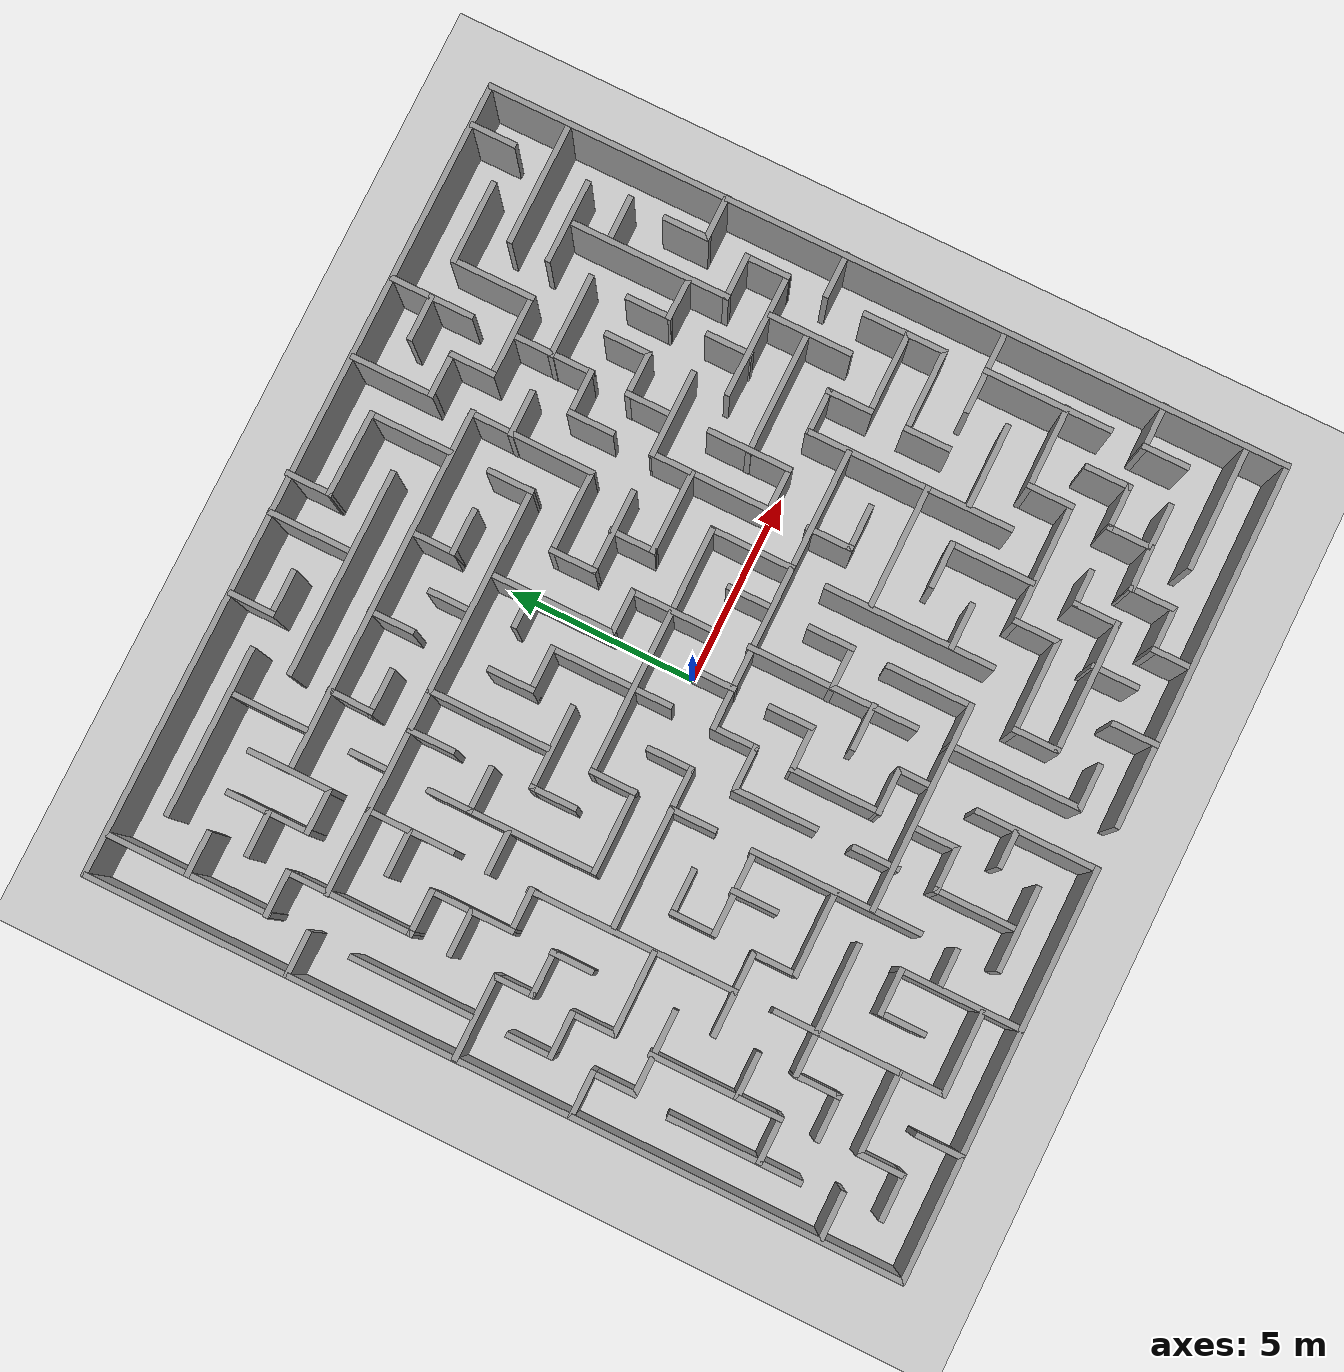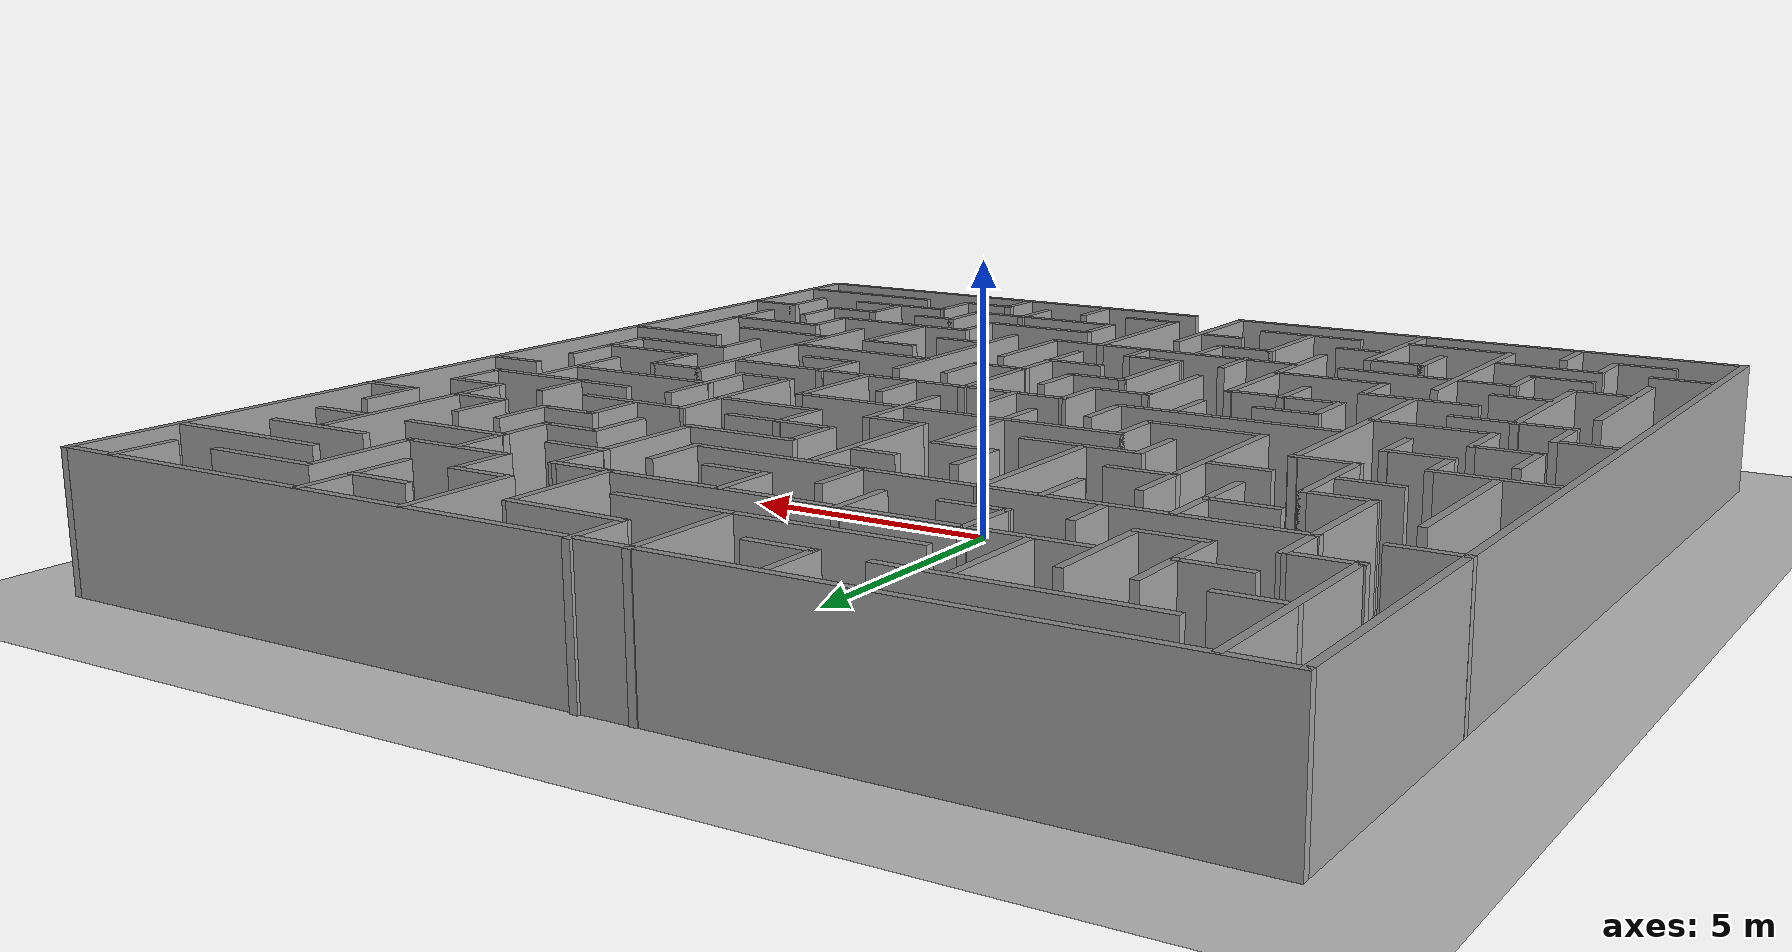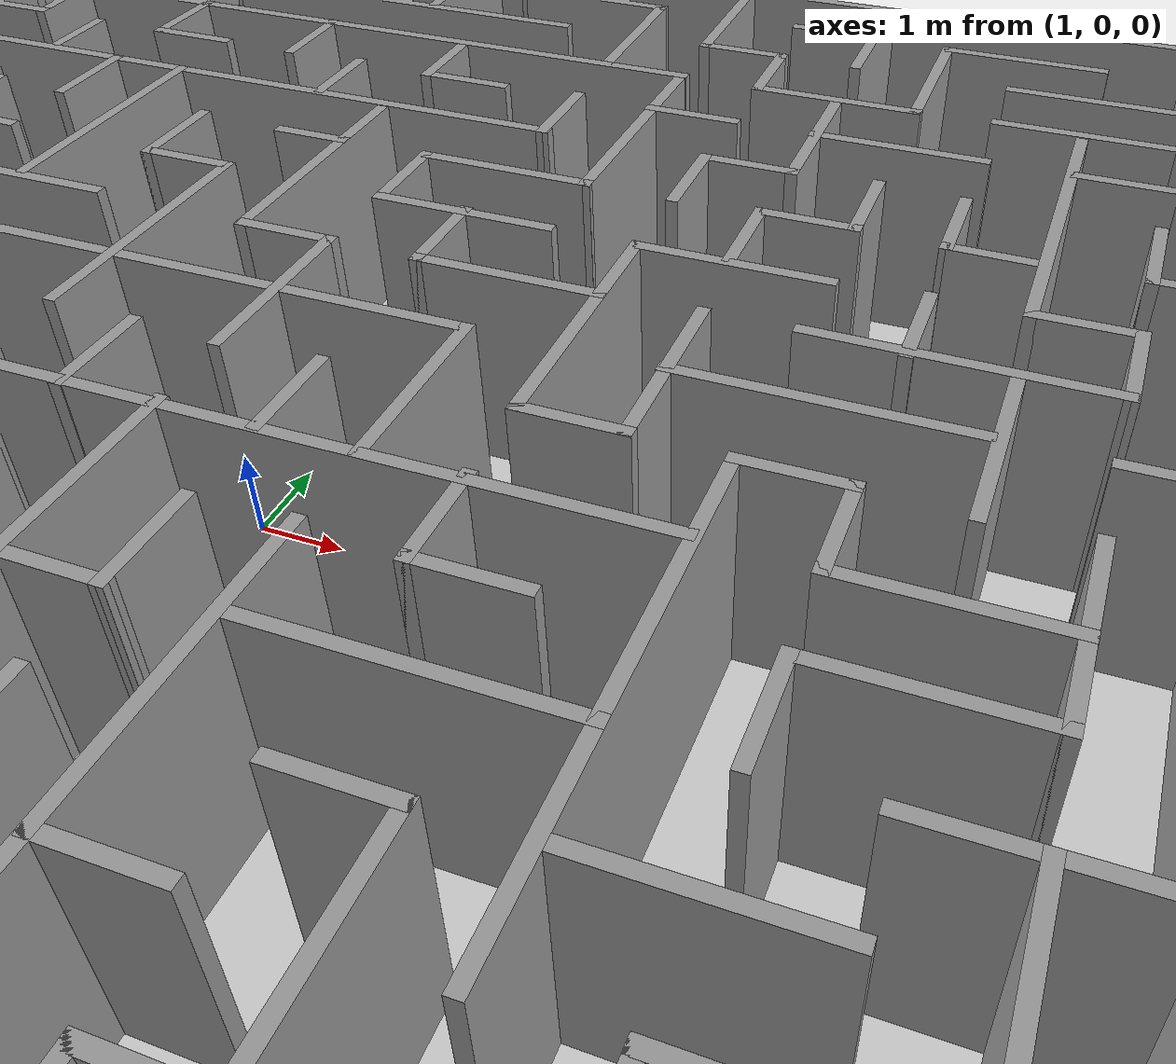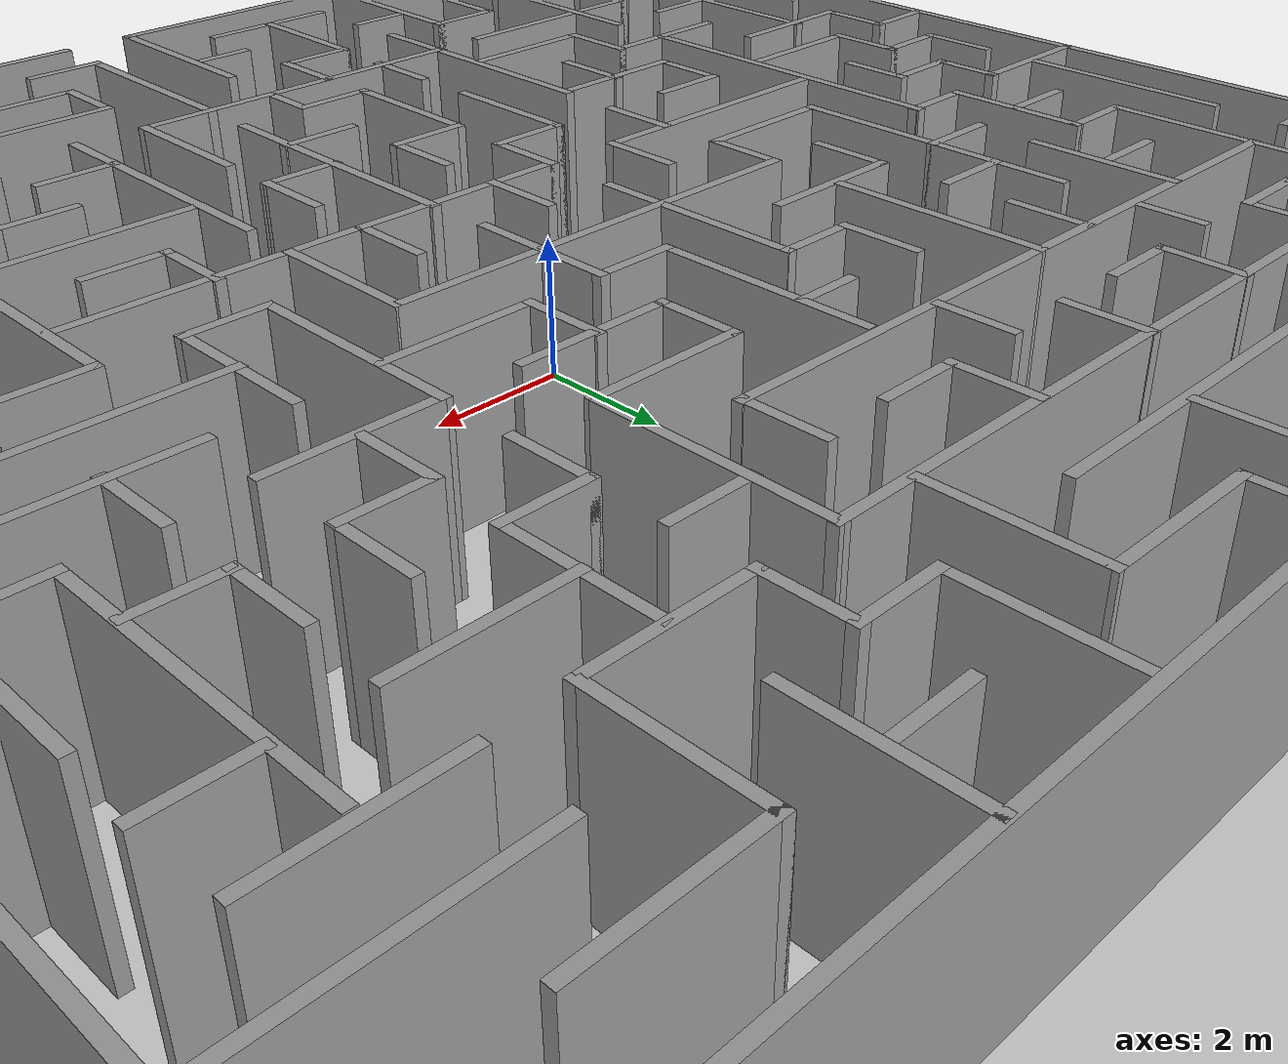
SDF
<sdf version="1.7">
 <world name="default">
  <light name="sun" type="directional">
   <pose>0 0 10 0 -0 0</pose>
   <diffuse>0.8 0.8 0.8 1</diffuse>
   <specular>0.2 0.2 0.2 1</specular>
   <attenuation>
    <range>1000</range>
    <constant>0.9</constant>
    <linear>0.01</linear>
    <quadratic>0.001</quadratic>
   </attenuation>
   <direction>-0.5 0.1 -0.9</direction>
   <spot><inner_angle>0</inner_angle><outer_angle>0</outer_angle><falloff>0</falloff></spot>
  </light>
  <model name="ground_plane">
   <static>1</static>
   <link name="link">
    <collision name="collision">
     <geometry><plane><normal>0 0 1</normal><size>100 100</size></plane></geometry>
     <surface><friction><ode><mu>100</mu><mu2>50</mu2></ode></friction></surface>
    </collision>
    <visual name="visual">
     <cast_shadows>0</cast_shadows>
     <geometry><plane><normal>0 0 1</normal><size>100 100</size></plane></geometry>
     <material>
      <script><uri>file://media/materials/scripts/gazebo.material</uri><name>Gazebo/Grey</name></script>
     </material>
    </visual>
   </link>
  </model>
  <gravity>0 0 -9.8</gravity>
  <magnetic_field>6e-06 2.3e-05 -4.2e-05</magnetic_field>
  <atmosphere type="adiabatic"/>
  <physics type="ode">
   <max_step_size>0.001</max_step_size>
   <real_time_factor>1</real_time_factor>
   <real_time_update_rate>1000</real_time_update_rate>
  </physics>
  <scene><ambient>0.4 0.4 0.4 1</ambient><background>0.7 0.7 0.7 1</background><shadows>1</shadows></scene>
  <audio><device>default</device></audio>
  <spherical_coordinates>
   <surface_model>EARTH_WGS84</surface_model>
   <latitude_deg>0</latitude_deg>
   <longitude_deg>0</longitude_deg>
   <elevation>0</elevation>
   <heading_deg>0</heading_deg>
  </spherical_coordinates>
  <model name="Maze_ej4">
   <pose>-0.00055 0.06164 0 0 -0 0</pose>
   <link name="Wall_100">
    <collision name="Wall_100_Collision">
     <geometry><box><size>1.25 0.15 2.5</size></box></geometry>
     <pose>0 0 1.25 0 -0 0</pose>
    </collision>
    <visual name="Wall_100_Visual">
     <pose>0 0 1.25 0 -0 0</pose>
     <geometry><box><size>1.25 0.15 2.5</size></box></geometry>
     <material>
      <script><uri>file://media/materials/scripts/gazebo.material</uri><name>Gazebo/Grey</name></script>
      <ambient>1 1 1 1</ambient>
     </material>
     <meta><layer>0</layer></meta>
    </visual>
    <pose>-7.51415 -6.98122 0 0 -0 -1.5708</pose>
   </link>
   <link name="Wall_101">
    <collision name="Wall_101_Collision">
     <geometry><box><size>1.25 0.15 2.5</size></box></geometry>
     <pose>0 0 1.25 0 -0 0</pose>
    </collision>
    <visual name="Wall_101_Visual">
     <pose>0 0 1.25 0 -0 0</pose>
     <geometry><box><size>1.25 0.15 2.5</size></box></geometry>
     <material>
      <script><uri>file://media/materials/scripts/gazebo.material</uri><name>Gazebo/Grey</name></script>
      <ambient>1 1 1 1</ambient>
     </material>
     <meta><layer>0</layer></meta>
    </visual>
    <pose>-8.06415 -7.53122 0 0 -0 3.14159</pose>
   </link>
   <link name="Wall_103">
    <collision name="Wall_103_Collision">
     <geometry><box><size>1.25 0.15 2.5</size></box></geometry>
     <pose>0 0 1.25 0 -0 0</pose>
    </collision>
    <visual name="Wall_103_Visual">
     <pose>0 0 1.25 0 -0 0</pose>
     <geometry><box><size>1.25 0.15 2.5</size></box></geometry>
     <material>
      <script><uri>file://media/materials/scripts/gazebo.material</uri><name>Gazebo/Grey</name></script>
      <ambient>1 1 1 1</ambient>
     </material>
     <meta><layer>0</layer></meta>
    </visual>
    <pose>-1.63534 -7.51693 0 0 -0 0</pose>
   </link>
   <link name="Wall_104">
    <collision name="Wall_104_Collision">
     <geometry><box><size>1.25 0.15 2.5</size></box></geometry>
     <pose>0 0 1.25 0 -0 0</pose>
    </collision>
    <visual name="Wall_104_Visual">
     <pose>0 0 1.25 0 -0 0</pose>
     <geometry><box><size>1.25 0.15 2.5</size></box></geometry>
     <material>
      <script><uri>file://media/materials/scripts/gazebo.material</uri><name>Gazebo/Grey</name></script>
      <ambient>1 1 1 1</ambient>
     </material>
     <meta><layer>0</layer></meta>
    </visual>
    <pose>-1.08534 -6.96694 0 0 -0 1.5708</pose>
   </link>
   <link name="Wall_106">
    <collision name="Wall_106_Collision">
     <geometry><box><size>1 0.15 2.5</size></box></geometry>
     <pose>0 0 1.25 0 -0 0</pose>
    </collision>
    <visual name="Wall_106_Visual">
     <pose>0 0 1.25 0 -0 0</pose>
     <geometry><box><size>1 0.15 2.5</size></box></geometry>
     <material>
      <script><uri>file://media/materials/scripts/gazebo.material</uri><name>Gazebo/Grey</name></script>
      <ambient>1 1 1 1</ambient>
     </material>
     <meta><layer>0</layer></meta>
    </visual>
    <pose>-3.6867 -8.55744 0 0 -0 3.14159</pose>
   </link>
   <link name="Wall_116">
    <collision name="Wall_116_Collision">
     <geometry><box><size>2.25 0.15 2.5</size></box></geometry>
     <pose>0 0 1.25 0 -0 0</pose>
    </collision>
    <visual name="Wall_116_Visual">
     <pose>0 0 1.25 0 -0 0</pose>
     <geometry><box><size>2.25 0.15 2.5</size></box></geometry>
     <material>
      <script><uri>file://media/materials/scripts/gazebo.material</uri><name>Gazebo/Grey</name></script>
      <ambient>1 1 1 1</ambient>
     </material>
     <meta><layer>0</layer></meta>
    </visual>
    <pose>8.55467 -5.36811 0 0 -0 3.14159</pose>
   </link>
   <link name="Wall_117">
    <collision name="Wall_117_Collision">
     <geometry><box><size>1.25 0.15 2.5</size></box></geometry>
     <pose>0 0 1.25 0 -0 0</pose>
    </collision>
    <visual name="Wall_117_Visual">
     <pose>0 0 1.25 0 -0 0</pose>
     <geometry><box><size>1.25 0.15 2.5</size></box></geometry>
     <material>
      <script><uri>file://media/materials/scripts/gazebo.material</uri><name>Gazebo/Grey</name></script>
      <ambient>1 1 1 1</ambient>
     </material>
     <meta><layer>0</layer></meta>
    </visual>
    <pose>7.50467 -5.91811 0 0 -0 -1.5708</pose>
   </link>
   <link name="Wall_118">
    <collision name="Wall_118_Collision">
     <geometry><box><size>3.25 0.15 2.5</size></box></geometry>
     <pose>0 0 1.25 0 -0 0</pose>
    </collision>
    <visual name="Wall_118_Visual">
     <pose>0 0 1.25 0 -0 0</pose>
     <geometry><box><size>3.25 0.15 2.5</size></box></geometry>
     <material>
      <script><uri>file://media/materials/scripts/gazebo.material</uri><name>Gazebo/Grey</name></script>
      <ambient>1 1 1 1</ambient>
     </material>
     <meta><layer>0</layer></meta>
    </visual>
    <pose>5.95467 -6.46811 0 0 -0 3.14159</pose>
   </link>
   <link name="Wall_119">
    <collision name="Wall_119_Collision">
     <geometry><box><size>1.25 0.15 2.5</size></box></geometry>
     <pose>0 0 1.25 0 -0 0</pose>
    </collision>
    <visual name="Wall_119_Visual">
     <pose>0 0 1.25 0 -0 0</pose>
     <geometry><box><size>1.25 0.15 2.5</size></box></geometry>
     <material>
      <script><uri>file://media/materials/scripts/gazebo.material</uri><name>Gazebo/Grey</name></script>
      <ambient>1 1 1 1</ambient>
     </material>
     <meta><layer>0</layer></meta>
    </visual>
    <pose>4.40467 -7.01811 0 0 -0 -1.5708</pose>
   </link>
   <link name="Wall_120">
    <collision name="Wall_120_Collision">
     <geometry><box><size>2.5 0.15 2.5</size></box></geometry>
     <pose>0 0 1.25 0 -0 0</pose>
    </collision>
    <visual name="Wall_120_Visual">
     <pose>0 0 1.25 0 -0 0</pose>
     <geometry><box><size>2.5 0.15 2.5</size></box></geometry>
     <material>
      <script><uri>file://media/materials/scripts/gazebo.material</uri><name>Gazebo/Grey</name></script>
      <ambient>1 1 1 1</ambient>
     </material>
     <meta><layer>0</layer></meta>
    </visual>
    <pose>3.22967 -7.56811 0 0 -0 3.14159</pose>
   </link>
   <link name="Wall_121">
    <collision name="Wall_121_Collision">
     <geometry><box><size>1.25 0.15 2.5</size></box></geometry>
     <pose>0 0 1.25 0 -0 0</pose>
    </collision>
    <visual name="Wall_121_Visual">
     <pose>0 0 1.25 0 -0 0</pose>
     <geometry><box><size>1.25 0.15 2.5</size></box></geometry>
     <material>
      <script><uri>file://media/materials/scripts/gazebo.material</uri><name>Gazebo/Grey</name></script>
      <ambient>1 1 1 1</ambient>
     </material>
     <meta><layer>0</layer></meta>
    </visual>
    <pose>2.05467 -8.11811 0 0 -0 -1.5708</pose>
   </link>
   <link name="Wall_122">
    <collision name="Wall_122_Collision">
     <geometry><box><size>3.5 0.15 2.5</size></box></geometry>
     <pose>0 0 1.25 0 -0 0</pose>
    </collision>
    <visual name="Wall_122_Visual">
     <pose>0 0 1.25 0 -0 0</pose>
     <geometry><box><size>3.5 0.15 2.5</size></box></geometry>
     <material>
      <script><uri>file://media/materials/scripts/gazebo.material</uri><name>Gazebo/Grey</name></script>
      <ambient>1 1 1 1</ambient>
     </material>
     <meta><layer>0</layer></meta>
    </visual>
    <pose>3.72967 -8.66811 0 0 -0 0</pose>
   </link>
   <link name="Wall_123">
    <collision name="Wall_123_Collision">
     <geometry><box><size>1.25 0.15 2.5</size></box></geometry>
     <pose>0 0 1.25 0 -0 0</pose>
    </collision>
    <visual name="Wall_123_Visual">
     <pose>0 0 1.25 0 -0 0</pose>
     <geometry><box><size>1.25 0.15 2.5</size></box></geometry>
     <material>
      <script><uri>file://media/materials/scripts/gazebo.material</uri><name>Gazebo/Grey</name></script>
      <ambient>1 1 1 1</ambient>
     </material>
     <meta><layer>0</layer></meta>
    </visual>
    <pose>5.40467 -8.11811 0 0 -0 1.5708</pose>
   </link>
   <link name="Wall_124">
    <collision name="Wall_124_Collision">
     <geometry><box><size>1 0.15 2.5</size></box></geometry>
     <pose>0 0 1.25 0 -0 0</pose>
    </collision>
    <visual name="Wall_124_Visual">
     <pose>0 0 1.25 0 -0 0</pose>
     <geometry><box><size>1 0.15 2.5</size></box></geometry>
     <material>
      <script><uri>file://media/materials/scripts/gazebo.material</uri><name>Gazebo/Grey</name></script>
      <ambient>1 1 1 1</ambient>
     </material>
     <meta><layer>0</layer></meta>
    </visual>
    <pose>5.82967 -7.56811 0 0 -0 0</pose>
   </link>
   <link name="Wall_129">
    <collision name="Wall_129_Collision">
     <geometry><box><size>1.25 0.15 2.5</size></box></geometry>
     <pose>0 0 1.25 0 -0 0</pose>
    </collision>
    <visual name="Wall_129_Visual">
     <pose>0 0 1.25 0 -0 0</pose>
     <geometry><box><size>1.25 0.15 2.5</size></box></geometry>
     <material>
      <script><uri>file://media/materials/scripts/gazebo.material</uri><name>Gazebo/Grey</name></script>
      <ambient>1 1 1 1</ambient>
     </material>
     <meta><layer>0</layer></meta>
    </visual>
    <pose>3.20667 -10.1551 0 0 -0 1.5708</pose>
   </link>
   <link name="Wall_131">
    <collision name="Wall_131_Collision">
     <geometry><box><size>1.25 0.15 2.5</size></box></geometry>
     <pose>0 0 1.25 0 -0 0</pose>
    </collision>
    <visual name="Wall_131_Visual">
     <pose>0 0 1.25 0 -0 0</pose>
     <geometry><box><size>1.25 0.15 2.5</size></box></geometry>
     <material>
      <script><uri>file://media/materials/scripts/gazebo.material</uri><name>Gazebo/Grey</name></script>
      <ambient>1 1 1 1</ambient>
     </material>
     <meta><layer>0</layer></meta>
    </visual>
    <pose>8.53131 -6.96633 0 0 -0 -1.5708</pose>
   </link>
   <link name="Wall_132">
    <collision name="Wall_132_Collision">
     <geometry><box><size>1.25 0.15 2.5</size></box></geometry>
     <pose>0 0 1.25 0 -0 0</pose>
    </collision>
    <visual name="Wall_132_Visual">
     <pose>0 0 1.25 0 -0 0</pose>
     <geometry><box><size>1.25 0.15 2.5</size></box></geometry>
     <material>
      <script><uri>file://media/materials/scripts/gazebo.material</uri><name>Gazebo/Grey</name></script>
      <ambient>1 1 1 1</ambient>
     </material>
     <meta><layer>0</layer></meta>
    </visual>
    <pose>7.98132 -7.51633 0 0 -0 3.14159</pose>
   </link>
   <link name="Wall_133">
    <collision name="Wall_133_Collision">
     <geometry><box><size>1.23183 0.15 2.5</size></box></geometry>
     <pose>0 0 1.25 0 -0 0</pose>
    </collision>
    <visual name="Wall_133_Visual">
     <pose>0 0 1.25 0 -0 0</pose>
     <geometry><box><size>1.23183 0.15 2.5</size></box></geometry>
     <material>
      <script><uri>file://media/materials/scripts/gazebo.material</uri><name>Gazebo/Grey</name></script>
      <ambient>1 1 1 1</ambient>
     </material>
     <meta><layer>0</layer></meta>
    </visual>
    <pose>7.43131 -8.05724 0 0 -0 -1.5708</pose>
   </link>
   <link name="Wall_134">
    <collision name="Wall_134_Collision">
     <geometry><box><size>1.25015 0.15 2.5</size></box></geometry>
     <pose>0 0 1.25 0 -0 0</pose>
    </collision>
    <visual name="Wall_134_Visual">
     <pose>0 0 1.25 0 -0 0</pose>
     <geometry><box><size>1.25015 0.15 2.5</size></box></geometry>
     <material>
      <script><uri>file://media/materials/scripts/gazebo.material</uri><name>Gazebo/Grey</name></script>
      <ambient>1 1 1 1</ambient>
     </material>
     <meta><layer>0</layer></meta>
    </visual>
    <pose>6.88131 -8.60724 0 0 -0 -3.12507</pose>
   </link>
   <link name="Wall_135">
    <collision name="Wall_135_Collision">
     <geometry><box><size>1.25 0.15 2.5</size></box></geometry>
     <pose>0 0 1.25 0 -0 0</pose>
    </collision>
    <visual name="Wall_135_Visual">
     <pose>0 0 1.25 0 -0 0</pose>
     <geometry><box><size>1.25 0.15 2.5</size></box></geometry>
     <material>
      <script><uri>file://media/materials/scripts/gazebo.material</uri><name>Gazebo/Grey</name></script>
      <ambient>1 1 1 1</ambient>
     </material>
     <meta><layer>0</layer></meta>
    </visual>
    <pose>6.33132 -9.16633 0 0 -0 -1.5708</pose>
   </link>
   <link name="Wall_136">
    <collision name="Wall_136_Collision">
     <geometry><box><size>1.25 0.15 2.5</size></box></geometry>
     <pose>0 0 1.25 0 -0 0</pose>
    </collision>
    <visual name="Wall_136_Visual">
     <pose>0 0 1.25 0 -0 0</pose>
     <geometry><box><size>1.25 0.15 2.5</size></box></geometry>
     <material>
      <script><uri>file://media/materials/scripts/gazebo.material</uri><name>Gazebo/Grey</name></script>
      <ambient>1 1 1 1</ambient>
     </material>
     <meta><layer>0</layer></meta>
    </visual>
    <pose>5.78132 -9.71633 0 0 -0 3.14159</pose>
   </link>
   <link name="Wall_137">
    <collision name="Wall_137_Collision">
     <geometry><box><size>1 0.15 2.5</size></box></geometry>
     <pose>0 0 1.25 0 -0 0</pose>
    </collision>
    <visual name="Wall_137_Visual">
     <pose>0 0 1.25 0 -0 0</pose>
     <geometry><box><size>1 0.15 2.5</size></box></geometry>
     <material>
      <script><uri>file://media/materials/scripts/gazebo.material</uri><name>Gazebo/Grey</name></script>
      <ambient>1 1 1 1</ambient>
     </material>
     <meta><layer>0</layer></meta>
    </visual>
    <pose>5.23132 -10.1413 0 0 -0 -1.5708</pose>
   </link>
   <link name="Wall_14">
    <collision name="Wall_14_Collision">
     <geometry><box><size>9.75 0.15 2.5</size></box></geometry>
     <pose>0 0 1.25 0 -0 0</pose>
    </collision>
    <visual name="Wall_14_Visual">
     <pose>0 0 1.25 0 -0 0</pose>
     <geometry><box><size>9.75 0.15 2.5</size></box></geometry>
     <material>
      <script><uri>file://media/materials/scripts/gazebo.material</uri><name>Gazebo/Grey</name></script>
      <ambient>1 1 1 1</ambient>
     </material>
     <meta><layer>0</layer></meta>
    </visual>
    <pose>5.86667 -10.7039 0 0 -0 0</pose>
   </link>
   <link name="Wall_141">
    <collision name="Wall_141_Collision">
     <geometry><box><size>1.25 0.15 2.5</size></box></geometry>
     <pose>0 0 1.25 0 -0 0</pose>
    </collision>
    <visual name="Wall_141_Visual">
     <pose>0 0 1.25 0 -0 0</pose>
     <geometry><box><size>1.25 0.15 2.5</size></box></geometry>
     <material>
      <script><uri>file://media/materials/scripts/gazebo.material</uri><name>Gazebo/Grey</name></script>
      <ambient>1 1 1 1</ambient>
     </material>
     <meta><layer>0</layer></meta>
    </visual>
    <pose>7.98132 -8.59816 0 0 -0 0</pose>
   </link>
   <link name="Wall_143">
    <collision name="Wall_143_Collision">
     <geometry><box><size>3.25 0.15 2.5</size></box></geometry>
     <pose>0 0 1.25 0 -0 0</pose>
    </collision>
    <visual name="Wall_143_Visual">
     <pose>0 0 1.25 0 -0 0</pose>
     <geometry><box><size>3.25 0.15 2.5</size></box></geometry>
     <material>
      <script><uri>file://media/materials/scripts/gazebo.material</uri><name>Gazebo/Grey</name></script>
      <ambient>1 1 1 1</ambient>
     </material>
     <meta><layer>0</layer></meta>
    </visual>
    <pose>8.97277 -9.65109 0 0 -0 0</pose>
   </link>
   <link name="Wall_145">
    <collision name="Wall_145_Collision">
     <geometry><box><size>1.25 0.15 2.5</size></box></geometry>
     <pose>0 0 1.25 0 -0 0</pose>
    </collision>
    <visual name="Wall_145_Visual">
     <pose>0 0 1.25 0 -0 0</pose>
     <geometry><box><size>1.25 0.15 2.5</size></box></geometry>
     <material>
      <script><uri>file://media/materials/scripts/gazebo.material</uri><name>Gazebo/Grey</name></script>
      <ambient>1 1 1 1</ambient>
     </material>
     <meta><layer>0</layer></meta>
    </visual>
    <pose>9.58534 -7.99255 0 0 -0 1.5708</pose>
   </link>
   <link name="Wall_146">
    <collision name="Wall_146_Collision">
     <geometry><box><size>1.25 0.15 2.5</size></box></geometry>
     <pose>0 0 1.25 0 -0 0</pose>
    </collision>
    <visual name="Wall_146_Visual">
     <pose>0 0 1.25 0 -0 0</pose>
     <geometry><box><size>1.25 0.15 2.5</size></box></geometry>
     <material>
      <script><uri>file://media/materials/scripts/gazebo.material</uri><name>Gazebo/Grey</name></script>
      <ambient>1 1 1 1</ambient>
     </material>
     <meta><layer>0</layer></meta>
    </visual>
    <pose>10.1353 -7.44255 0 0 -0 0</pose>
   </link>
   <link name="Wall_148">
    <collision name="Wall_148_Collision">
     <geometry><box><size>3.42111 0.15 2.5</size></box></geometry>
     <pose>0 0 1.25 0 -0 0</pose>
    </collision>
    <visual name="Wall_148_Visual">
     <pose>0 0 1.25 0 -0 0</pose>
     <geometry><box><size>3.42111 0.15 2.5</size></box></geometry>
     <material>
      <script><uri>file://media/materials/scripts/gazebo.material</uri><name>Gazebo/Grey</name></script>
      <ambient>1 1 1 1</ambient>
     </material>
     <meta><layer>0</layer></meta>
    </visual>
    <pose>9.58534 -4.87164 0 0 -0 1.5708</pose>
   </link>
   <link name="Wall_15">
    <collision name="Wall_15_Collision">
     <geometry><box><size>21.5 0.15 2.5</size></box></geometry>
     <pose>0 0 1.25 0 -0 0</pose>
    </collision>
    <visual name="Wall_15_Visual">
     <pose>0 0 1.25 0 -0 0</pose>
     <geometry><box><size>21.5 0.15 2.5</size></box></geometry>
     <material>
      <script><uri>file://media/materials/scripts/gazebo.material</uri><name>Gazebo/Grey</name></script>
      <ambient>1 1 1 1</ambient>
     </material>
     <meta><layer>0</layer></meta>
    </visual>
    <pose>10.6667 -0.028895 0 0 -0 1.5708</pose>
   </link>
   <link name="Wall_150">
    <collision name="Wall_150_Collision">
     <geometry><box><size>2.25 0.15 2.5</size></box></geometry>
     <pose>0 0 1.25 0 -0 0</pose>
    </collision>
    <visual name="Wall_150_Visual">
     <pose>0 0 1.25 0 -0 0</pose>
     <geometry><box><size>2.25 0.15 2.5</size></box></geometry>
     <material>
      <script><uri>file://media/materials/scripts/gazebo.material</uri><name>Gazebo/Grey</name></script>
      <ambient>1 1 1 1</ambient>
     </material>
     <meta><layer>0</layer></meta>
    </visual>
    <pose>9.56314 -3.23608 0 0 -0 0</pose>
   </link>
   <link name="Wall_152">
    <collision name="Wall_152_Collision">
     <geometry><box><size>1.25 0.15 2.5</size></box></geometry>
     <pose>0 0 1.25 0 -0 0</pose>
    </collision>
    <visual name="Wall_152_Visual">
     <pose>0 0 1.25 0 -0 0</pose>
     <geometry><box><size>1.25 0.15 2.5</size></box></geometry>
     <material>
      <script><uri>file://media/materials/scripts/gazebo.material</uri><name>Gazebo/Grey</name></script>
      <ambient>1 1 1 1</ambient>
     </material>
     <meta><layer>0</layer></meta>
    </visual>
    <pose>4.86522 -4.30828 0 0 -0 0</pose>
   </link>
   <link name="Wall_153">
    <collision name="Wall_153_Collision">
     <geometry><box><size>2.25 0.15 2.5</size></box></geometry>
     <pose>0 0 1.25 0 -0 0</pose>
    </collision>
    <visual name="Wall_153_Visual">
     <pose>0 0 1.25 0 -0 0</pose>
     <geometry><box><size>2.25 0.15 2.5</size></box></geometry>
     <material>
      <script><uri>file://media/materials/scripts/gazebo.material</uri><name>Gazebo/Grey</name></script>
      <ambient>1 1 1 1</ambient>
     </material>
     <meta><layer>0</layer></meta>
    </visual>
    <pose>5.41522 -5.35828 0 0 -0 -1.5708</pose>
   </link>
   <link name="Wall_155">
    <collision name="Wall_155_Collision">
     <geometry><box><size>4.5 0.15 2.5</size></box></geometry>
     <pose>0 0 1.25 0 -0 0</pose>
    </collision>
    <visual name="Wall_155_Visual">
     <pose>0 0 1.25 0 -0 0</pose>
     <geometry><box><size>4.5 0.15 2.5</size></box></geometry>
     <material>
      <script><uri>file://media/materials/scripts/gazebo.material</uri><name>Gazebo/Grey</name></script>
      <ambient>1 1 1 1</ambient>
     </material>
     <meta><layer>0</layer></meta>
    </visual>
    <pose>3.17033 -4.2595 0 0 -0 1.5708</pose>
   </link>
   <link name="Wall_157">
    <collision name="Wall_157_Collision">
     <geometry><box><size>5.5 0.15 2.5</size></box></geometry>
     <pose>0 0 1.25 0 -0 0</pose>
    </collision>
    <visual name="Wall_157_Visual">
     <pose>0 0 1.25 0 -0 0</pose>
     <geometry><box><size>5.5 0.15 2.5</size></box></geometry>
     <material>
      <script><uri>file://media/materials/scripts/gazebo.material</uri><name>Gazebo/Grey</name></script>
      <ambient>1 1 1 1</ambient>
     </material>
     <meta><layer>0</layer></meta>
    </visual>
    <pose>6.36875 -2.72365 0 0 -0 1.5708</pose>
   </link>
   <link name="Wall_158">
    <collision name="Wall_158_Collision">
     <geometry><box><size>1.25 0.15 2.5</size></box></geometry>
     <pose>0 0 1.25 0 -0 0</pose>
    </collision>
    <visual name="Wall_158_Visual">
     <pose>0 0 1.25 0 -0 0</pose>
     <geometry><box><size>1.25 0.15 2.5</size></box></geometry>
     <material>
      <script><uri>file://media/materials/scripts/gazebo.material</uri><name>Gazebo/Grey</name></script>
      <ambient>1 1 1 1</ambient>
     </material>
     <meta><layer>0</layer></meta>
    </visual>
    <pose>6.91875 -0.048649 0 0 -0 0</pose>
   </link>
   <link name="Wall_159">
    <collision name="Wall_159_Collision">
     <geometry><box><size>1.25 0.15 2.5</size></box></geometry>
     <pose>0 0 1.25 0 -0 0</pose>
    </collision>
    <visual name="Wall_159_Visual">
     <pose>0 0 1.25 0 -0 0</pose>
     <geometry><box><size>1.25 0.15 2.5</size></box></geometry>
     <material>
      <script><uri>file://media/materials/scripts/gazebo.material</uri><name>Gazebo/Grey</name></script>
      <ambient>1 1 1 1</ambient>
     </material>
     <meta><layer>0</layer></meta>
    </visual>
    <pose>7.46875 -0.598649 0 0 -0 -1.5708</pose>
   </link>
   <link name="Wall_16">
    <collision name="Wall_16_Collision">
     <geometry><box><size>21.5 0.15 2.5</size></box></geometry>
     <pose>0 0 1.25 0 -0 0</pose>
    </collision>
    <visual name="Wall_16_Visual">
     <pose>0 0 1.25 0 -0 0</pose>
     <geometry><box><size>21.5 0.15 2.5</size></box></geometry>
     <material>
      <script><uri>file://media/materials/scripts/gazebo.material</uri><name>Gazebo/Grey</name></script>
      <ambient>1 1 1 1</ambient>
     </material>
     <meta><layer>0</layer></meta>
    </visual>
    <pose>-0.008328 10.6461 0 0 -0 3.14159</pose>
   </link>
   <link name="Wall_160">
    <collision name="Wall_160_Collision">
     <geometry><box><size>2.25 0.15 2.5</size></box></geometry>
     <pose>0 0 1.25 0 -0 0</pose>
    </collision>
    <visual name="Wall_160_Visual">
     <pose>0 0 1.25 0 -0 0</pose>
     <geometry><box><size>2.25 0.15 2.5</size></box></geometry>
     <material>
      <script><uri>file://media/materials/scripts/gazebo.material</uri><name>Gazebo/Grey</name></script>
      <ambient>1 1 1 1</ambient>
     </material>
     <meta><layer>0</layer></meta>
    </visual>
    <pose>8.51875 -1.14865 0 0 -0 0</pose>
   </link>
   <link name="Wall_162">
    <collision name="Wall_162_Collision">
     <geometry><box><size>2.25 0.15 2.5</size></box></geometry>
     <pose>0 0 1.25 0 -0 0</pose>
    </collision>
    <visual name="Wall_162_Visual">
     <pose>0 0 1.25 0 -0 0</pose>
     <geometry><box><size>2.25 0.15 2.5</size></box></geometry>
     <material>
      <script><uri>file://media/materials/scripts/gazebo.material</uri><name>Gazebo/Grey</name></script>
      <ambient>1 1 1 1</ambient>
     </material>
     <meta><layer>0</layer></meta>
    </visual>
    <pose>7.51766 -4.27193 0 0 -0 3.14159</pose>
   </link>
   <link name="Wall_164">
    <collision name="Wall_164_Collision">
     <geometry><box><size>3.25 0.15 2.5</size></box></geometry>
     <pose>0 0 1.25 0 -0 0</pose>
    </collision>
    <visual name="Wall_164_Visual">
     <pose>0 0 1.25 0 -0 0</pose>
     <geometry><box><size>3.25 0.15 2.5</size></box></geometry>
     <material>
      <script><uri>file://media/materials/scripts/gazebo.material</uri><name>Gazebo/Grey</name></script>
      <ambient>1 1 1 1</ambient>
     </material>
     <meta><layer>0</layer></meta>
    </visual>
    <pose>4.81875 -3.19974 0 0 -0 3.14159</pose>
   </link>
   <link name="Wall_166">
    <collision name="Wall_166_Collision">
     <geometry><box><size>1.25 0.15 2.5</size></box></geometry>
     <pose>0 0 1.25 0 -0 0</pose>
    </collision>
    <visual name="Wall_166_Visual">
     <pose>0 0 1.25 0 -0 0</pose>
     <geometry><box><size>1.25 0.15 2.5</size></box></geometry>
     <material>
      <script><uri>file://media/materials/scripts/gazebo.material</uri><name>Gazebo/Grey</name></script>
      <ambient>1 1 1 1</ambient>
     </material>
     <meta><layer>0</layer></meta>
    </visual>
    <pose>3.72887 -5.3623 0 0 -0 3.14159</pose>
   </link>
   <link name="Wall_168">
    <collision name="Wall_168_Collision">
     <geometry><box><size>1.25 0.15 2.5</size></box></geometry>
     <pose>0 0 1.25 0 -0 0</pose>
    </collision>
    <visual name="Wall_168_Visual">
     <pose>0 0 1.25 0 -0 0</pose>
     <geometry><box><size>1.25 0.15 2.5</size></box></geometry>
     <material>
      <script><uri>file://media/materials/scripts/gazebo.material</uri><name>Gazebo/Grey</name></script>
      <ambient>1 1 1 1</ambient>
     </material>
     <meta><layer>0</layer></meta>
    </visual>
    <pose>-0.00992 -2.67754 0 0 -0 -1.5708</pose>
   </link>
   <link name="Wall_17">
    <collision name="Wall_17_Collision">
     <geometry><box><size>21.5 0.15 2.5</size></box></geometry>
     <pose>0 0 1.25 0 -0 0</pose>
    </collision>
    <visual name="Wall_17_Visual">
     <pose>0 0 1.25 0 -0 0</pose>
     <geometry><box><size>21.5 0.15 2.5</size></box></geometry>
     <material>
      <script><uri>file://media/materials/scripts/gazebo.material</uri><name>Gazebo/Grey</name></script>
      <ambient>1 1 1 1</ambient>
     </material>
     <meta><layer>0</layer></meta>
    </visual>
    <pose>-10.6833 -0.028895 0 0 -0 -1.5708</pose>
   </link>
   <link name="Wall_171">
    <collision name="Wall_171_Collision">
     <geometry><box><size>1.25 0.15 2.5</size></box></geometry>
     <pose>0 0 1.25 0 -0 0</pose>
    </collision>
    <visual name="Wall_171_Visual">
     <pose>0 0 1.25 0 -0 0</pose>
     <geometry><box><size>1.25 0.15 2.5</size></box></geometry>
     <material>
      <script><uri>file://media/materials/scripts/gazebo.material</uri><name>Gazebo/Grey</name></script>
      <ambient>1 1 1 1</ambient>
     </material>
     <meta><layer>0</layer></meta>
    </visual>
    <pose>-0.55992 -3.22754 0 0 -0 3.14159</pose>
   </link>
   <link name="Wall_172">
    <collision name="Wall_172_Collision">
     <geometry><box><size>2.43059 0.15 2.5</size></box></geometry>
     <pose>0 0 1.25 0 -0 0</pose>
    </collision>
    <visual name="Wall_172_Visual">
     <pose>0 0 1.25 0 -0 0</pose>
     <geometry><box><size>2.43059 0.15 2.5</size></box></geometry>
     <material>
      <script><uri>file://media/materials/scripts/gazebo.material</uri><name>Gazebo/Grey</name></script>
      <ambient>1 1 1 1</ambient>
     </material>
     <meta><layer>0</layer></meta>
    </visual>
    <pose>-1.11419 -4.36761 0 0 -0 -1.57454</pose>
   </link>
   <link name="Wall_173">
    <collision name="Wall_173_Collision">
     <geometry><box><size>1.25 0.15 2.5</size></box></geometry>
     <pose>0 0 1.25 0 -0 0</pose>
    </collision>
    <visual name="Wall_173_Visual">
     <pose>0 0 1.25 0 -0 0</pose>
     <geometry><box><size>1.25 0.15 2.5</size></box></geometry>
     <material>
      <script><uri>file://media/materials/scripts/gazebo.material</uri><name>Gazebo/Grey</name></script>
      <ambient>1 1 1 1</ambient>
     </material>
     <meta><layer>0</layer></meta>
    </visual>
    <pose>-0.568463 -5.50769 0 0 -0 0</pose>
   </link>
   <link name="Wall_174">
    <collision name="Wall_174_Collision">
     <geometry><box><size>1 0.15 2.5</size></box></geometry>
     <pose>0 0 1.25 0 -0 0</pose>
    </collision>
    <visual name="Wall_174_Visual">
     <pose>0 0 1.25 0 -0 0</pose>
     <geometry><box><size>1 0.15 2.5</size></box></geometry>
     <material>
      <script><uri>file://media/materials/scripts/gazebo.material</uri><name>Gazebo/Grey</name></script>
      <ambient>1 1 1 1</ambient>
     </material>
     <meta><layer>0</layer></meta>
    </visual>
    <pose>-0.018463 -5.93269 0 0 -0 -1.5708</pose>
   </link>
   <link name="Wall_176">
    <collision name="Wall_176_Collision">
     <geometry><box><size>4.5 0.15 2.5</size></box></geometry>
     <pose>0 0 1.25 0 -0 0</pose>
    </collision>
    <visual name="Wall_176_Visual">
     <pose>0 0 1.25 0 -0 0</pose>
     <geometry><box><size>4.5 0.15 2.5</size></box></geometry>
     <material>
      <script><uri>file://media/materials/scripts/gazebo.material</uri><name>Gazebo/Grey</name></script>
      <ambient>1 1 1 1</ambient>
     </material>
     <meta><layer>0</layer></meta>
    </visual>
    <pose>1.06228 -3.24182 0 0 -0 1.5708</pose>
   </link>
   <link name="Wall_178">
    <collision name="Wall_178_Collision">
     <geometry><box><size>1.25 0.15 2.5</size></box></geometry>
     <pose>0 0 1.25 0 -0 0</pose>
    </collision>
    <visual name="Wall_178_Visual">
     <pose>0 0 1.25 0 -0 0</pose>
     <geometry><box><size>1.25 0.15 2.5</size></box></geometry>
     <material>
      <script><uri>file://media/materials/scripts/gazebo.material</uri><name>Gazebo/Grey</name></script>
      <ambient>1 1 1 1</ambient>
     </material>
     <meta><layer>0</layer></meta>
    </visual>
    <pose>2.1163 -2.69571 0 0 -0 -1.5708</pose>
   </link>
   <link name="Wall_179">
    <collision name="Wall_179_Collision">
     <geometry><box><size>1.22224 0.15 2.5</size></box></geometry>
     <pose>0 0 1.25 0 -0 0</pose>
    </collision>
    <visual name="Wall_179_Visual">
     <pose>0 0 1.25 0 -0 0</pose>
     <geometry><box><size>1.22224 0.15 2.5</size></box></geometry>
     <material>
      <script><uri>file://media/materials/scripts/gazebo.material</uri><name>Gazebo/Grey</name></script>
      <ambient>1 1 1 1</ambient>
     </material>
     <meta><layer>0</layer></meta>
    </visual>
    <pose>1.5802 -3.2409 0 0 -0 3.13261</pose>
   </link>
   <link name="Wall_18">
    <collision name="Wall_18_Collision">
     <geometry><box><size>10.75 0.15 2.5</size></box></geometry>
     <pose>0 0 1.25 0 -0 0</pose>
    </collision>
    <visual name="Wall_18_Visual">
     <pose>0 0 1.25 0 -0 0</pose>
     <geometry><box><size>10.75 0.15 2.5</size></box></geometry>
     <material>
      <script><uri>file://media/materials/scripts/gazebo.material</uri><name>Gazebo/Grey</name></script>
      <ambient>1 1 1 1</ambient>
     </material>
     <meta><layer>0</layer></meta>
    </visual>
    <pose>-5.38333 -10.7039 0 0 -0 0</pose>
   </link>
   <link name="Wall_181">
    <collision name="Wall_181_Collision">
     <geometry><box><size>1.25 0.15 2.5</size></box></geometry>
     <pose>0 0 1.25 0 -0 0</pose>
    </collision>
    <visual name="Wall_181_Visual">
     <pose>0 0 1.25 0 -0 0</pose>
     <geometry><box><size>1.25 0.15 2.5</size></box></geometry>
     <material>
      <script><uri>file://media/materials/scripts/gazebo.material</uri><name>Gazebo/Grey</name></script>
      <ambient>1 1 1 1</ambient>
     </material>
     <meta><layer>0</layer></meta>
    </visual>
    <pose>0.54008 -4.30828 0 0 -0 0</pose>
   </link>
   <link name="Wall_183">
    <collision name="Wall_183_Collision">
     <geometry><box><size>1.25 0.15 2.5</size></box></geometry>
     <pose>0 0 1.25 0 -0 0</pose>
    </collision>
    <visual name="Wall_183_Visual">
     <pose>0 0 1.25 0 -0 0</pose>
     <geometry><box><size>1.25 0.15 2.5</size></box></geometry>
     <material>
      <script><uri>file://media/materials/scripts/gazebo.material</uri><name>Gazebo/Grey</name></script>
      <ambient>1 1 1 1</ambient>
     </material>
     <meta><layer>0</layer></meta>
    </visual>
    <pose>-2.13614 -5.9123 0 0 -0 -1.5708</pose>
   </link>
   <link name="Wall_185">
    <collision name="Wall_185_Collision">
     <geometry><box><size>1.25 0.15 2.5</size></box></geometry>
     <pose>0 0 1.25 0 -0 0</pose>
    </collision>
    <visual name="Wall_185_Visual">
     <pose>0 0 1.25 0 -0 0</pose>
     <geometry><box><size>1.25 0.15 2.5</size></box></geometry>
     <material>
      <script><uri>file://media/materials/scripts/gazebo.material</uri><name>Gazebo/Grey</name></script>
      <ambient>1 1 1 1</ambient>
     </material>
     <meta><layer>0</layer></meta>
    </visual>
    <pose>-4.84871 -2.18206 0 0 -0 3.14159</pose>
   </link>
   <link name="Wall_186">
    <collision name="Wall_186_Collision">
     <geometry><box><size>1.25 0.15 2.5</size></box></geometry>
     <pose>0 0 1.25 0 -0 0</pose>
    </collision>
    <visual name="Wall_186_Visual">
     <pose>0 0 1.25 0 -0 0</pose>
     <geometry><box><size>1.25 0.15 2.5</size></box></geometry>
     <material>
      <script><uri>file://media/materials/scripts/gazebo.material</uri><name>Gazebo/Grey</name></script>
      <ambient>1 1 1 1</ambient>
     </material>
     <meta><layer>0</layer></meta>
    </visual>
    <pose>-5.39871 -2.73206 0 0 -0 -1.5708</pose>
   </link>
   <link name="Wall_187">
    <collision name="Wall_187_Collision">
     <geometry><box><size>2.25 0.15 2.5</size></box></geometry>
     <pose>0 0 1.25 0 -0 0</pose>
    </collision>
    <visual name="Wall_187_Visual">
     <pose>0 0 1.25 0 -0 0</pose>
     <geometry><box><size>2.25 0.15 2.5</size></box></geometry>
     <material>
      <script><uri>file://media/materials/scripts/gazebo.material</uri><name>Gazebo/Grey</name></script>
      <ambient>1 1 1 1</ambient>
     </material>
     <meta><layer>0</layer></meta>
    </visual>
    <pose>-4.34871 -3.28206 0 0 -0 0</pose>
   </link>
   <link name="Wall_189">
    <collision name="Wall_189_Collision">
     <geometry><box><size>1.25 0.15 2.5</size></box></geometry>
     <pose>0 0 1.25 0 -0 0</pose>
    </collision>
    <visual name="Wall_189_Visual">
     <pose>0 0 1.25 0 -0 0</pose>
     <geometry><box><size>1.25 0.15 2.5</size></box></geometry>
     <material>
      <script><uri>file://media/materials/scripts/gazebo.material</uri><name>Gazebo/Grey</name></script>
      <ambient>1 1 1 1</ambient>
     </material>
     <meta><layer>0</layer></meta>
    </visual>
    <pose>-4.29871 -3.78608 0 0 -0 -1.5708</pose>
   </link>
   <link name="Wall_19">
    <collision name="Wall_19_Collision">
     <geometry><box><size>3.25 0.15 2.5</size></box></geometry>
     <pose>0 0 1.25 0 -0 0</pose>
    </collision>
    <visual name="Wall_19_Visual">
     <pose>0 0 1.25 0 -0 0</pose>
     <geometry><box><size>3.25 0.15 2.5</size></box></geometry>
     <material>
      <script><uri>file://media/materials/scripts/gazebo.material</uri><name>Gazebo/Grey</name></script>
      <ambient>1 1 1 1</ambient>
     </material>
     <meta><layer>0</layer></meta>
    </visual>
    <pose>-0.083328 -9.1539 0 0 -0 1.5708</pose>
   </link>
   <link name="Wall_191">
    <collision name="Wall_191_Collision">
     <geometry><box><size>2.25 0.15 2.5</size></box></geometry>
     <pose>0 0 1.25 0 -0 0</pose>
    </collision>
    <visual name="Wall_191_Visual">
     <pose>0 0 1.25 0 -0 0</pose>
     <geometry><box><size>2.25 0.15 2.5</size></box></geometry>
     <material>
      <script><uri>file://media/materials/scripts/gazebo.material</uri><name>Gazebo/Grey</name></script>
      <ambient>1 1 1 1</ambient>
     </material>
     <meta><layer>0</layer></meta>
    </visual>
    <pose>-2.1319 -3.27188 0 0 -0 1.5708</pose>
   </link>
   <link name="Wall_192">
    <collision name="Wall_192_Collision">
     <geometry><box><size>1.25 0.15 2.5</size></box></geometry>
     <pose>0 0 1.25 0 -0 0</pose>
    </collision>
    <visual name="Wall_192_Visual">
     <pose>0 0 1.25 0 -0 0</pose>
     <geometry><box><size>1.25 0.15 2.5</size></box></geometry>
     <material>
      <script><uri>file://media/materials/scripts/gazebo.material</uri><name>Gazebo/Grey</name></script>
      <ambient>1 1 1 1</ambient>
     </material>
     <meta><layer>0</layer></meta>
    </visual>
    <pose>-1.5819 -2.22188 0 0 -0 0</pose>
   </link>
   <link name="Wall_193">
    <collision name="Wall_193_Collision">
     <geometry><box><size>1.25 0.15 2.5</size></box></geometry>
     <pose>0 0 1.25 0 -0 0</pose>
    </collision>
    <visual name="Wall_193_Visual">
     <pose>0 0 1.25 0 -0 0</pose>
     <geometry><box><size>1.25 0.15 2.5</size></box></geometry>
     <material>
      <script><uri>file://media/materials/scripts/gazebo.material</uri><name>Gazebo/Grey</name></script>
      <ambient>1 1 1 1</ambient>
     </material>
     <meta><layer>0</layer></meta>
    </visual>
    <pose>-1.0319 -1.67188 0 0 -0 1.5708</pose>
   </link>
   <link name="Wall_194">
    <collision name="Wall_194_Collision">
     <geometry><box><size>7.5 0.15 2.5</size></box></geometry>
     <pose>0 0 1.25 0 -0 0</pose>
    </collision>
    <visual name="Wall_194_Visual">
     <pose>0 0 1.25 0 -0 0</pose>
     <geometry><box><size>7.5 0.15 2.5</size></box></geometry>
     <material>
      <script><uri>file://media/materials/scripts/gazebo.material</uri><name>Gazebo/Grey</name></script>
      <ambient>1 1 1 1</ambient>
     </material>
     <meta><layer>0</layer></meta>
    </visual>
    <pose>2.6431 -1.12188 0 0 -0 0</pose>
   </link>
   <link name="Wall_196">
    <collision name="Wall_196_Collision">
     <geometry><box><size>1.25 0.15 2.5</size></box></geometry>
     <pose>0 0 1.25 0 -0 0</pose>
    </collision>
    <visual name="Wall_196_Visual">
     <pose>0 0 1.25 0 -0 0</pose>
     <geometry><box><size>1.25 0.15 2.5</size></box></geometry>
     <material>
      <script><uri>file://media/materials/scripts/gazebo.material</uri><name>Gazebo/Grey</name></script>
      <ambient>1 1 1 1</ambient>
     </material>
     <meta><layer>0</layer></meta>
    </visual>
    <pose>4.25677 -1.61398 0 0 -0 -1.5708</pose>
   </link>
   <link name="Wall_197">
    <collision name="Wall_197_Collision">
     <geometry><box><size>1.25 0.15 2.5</size></box></geometry>
     <pose>0 0 1.25 0 -0 0</pose>
    </collision>
    <visual name="Wall_197_Visual">
     <pose>0 0 1.25 0 -0 0</pose>
     <geometry><box><size>1.25 0.15 2.5</size></box></geometry>
     <material>
      <script><uri>file://media/materials/scripts/gazebo.material</uri><name>Gazebo/Grey</name></script>
      <ambient>1 1 1 1</ambient>
     </material>
     <meta><layer>0</layer></meta>
    </visual>
    <pose>4.80677 -2.16398 0 0 -0 0</pose>
   </link>
   <link name="Wall_199">
    <collision name="Wall_199_Collision">
     <geometry><box><size>1.25 0.15 2.5</size></box></geometry>
     <pose>0 0 1.25 0 -0 0</pose>
    </collision>
    <visual name="Wall_199_Visual">
     <pose>0 0 1.25 0 -0 0</pose>
     <geometry><box><size>1.25 0.15 2.5</size></box></geometry>
     <material>
      <script><uri>file://media/materials/scripts/gazebo.material</uri><name>Gazebo/Grey</name></script>
      <ambient>1 1 1 1</ambient>
     </material>
     <meta><layer>0</layer></meta>
    </visual>
    <pose>7.467 -2.67532 0 0 -0 1.5708</pose>
   </link>
   <link name="Wall_200">
    <collision name="Wall_200_Collision">
     <geometry><box><size>2.25 0.15 2.5</size></box></geometry>
     <pose>0 0 1.25 0 -0 0</pose>
    </collision>
    <visual name="Wall_200_Visual">
     <pose>0 0 1.25 0 -0 0</pose>
     <geometry><box><size>2.25 0.15 2.5</size></box></geometry>
     <material>
      <script><uri>file://media/materials/scripts/gazebo.material</uri><name>Gazebo/Grey</name></script>
      <ambient>1 1 1 1</ambient>
     </material>
     <meta><layer>0</layer></meta>
    </visual>
    <pose>8.517 -2.12532 0 0 -0 0</pose>
   </link>
   <link name="Wall_201">
    <collision name="Wall_201_Collision">
     <geometry><box><size>2.25 0.15 2.5</size></box></geometry>
     <pose>0 0 1.25 0 -0 0</pose>
    </collision>
    <visual name="Wall_201_Visual">
     <pose>0 0 1.25 0 -0 0</pose>
     <geometry><box><size>2.25 0.15 2.5</size></box></geometry>
     <material>
      <script><uri>file://media/materials/scripts/gazebo.material</uri><name>Gazebo/Grey</name></script>
      <ambient>1 1 1 1</ambient>
     </material>
     <meta><layer>0</layer></meta>
    </visual>
    <pose>9.567 -1.07532 0 0 -0 1.5708</pose>
   </link>
   <link name="Wall_205">
    <collision name="Wall_205_Collision">
     <geometry><box><size>1.25 0.15 2.5</size></box></geometry>
     <pose>0 0 1.25 0 -0 0</pose>
    </collision>
    <visual name="Wall_205_Visual">
     <pose>0 0 1.25 0 -0 0</pose>
     <geometry><box><size>1.25 0.15 2.5</size></box></geometry>
     <material>
      <script><uri>file://media/materials/scripts/gazebo.material</uri><name>Gazebo/Grey</name></script>
      <ambient>1 1 1 1</ambient>
     </material>
     <meta><layer>0</layer></meta>
    </visual>
    <pose>-2.16368 -0.533309 0 0 -0 -1.5708</pose>
   </link>
   <link name="Wall_206">
    <collision name="Wall_206_Collision">
     <geometry><box><size>4.25 0.15 2.5</size></box></geometry>
     <pose>0 0 1.25 0 -0 0</pose>
    </collision>
    <visual name="Wall_206_Visual">
     <pose>0 0 1.25 0 -0 0</pose>
     <geometry><box><size>4.25 0.15 2.5</size></box></geometry>
     <material>
      <script><uri>file://media/materials/scripts/gazebo.material</uri><name>Gazebo/Grey</name></script>
      <ambient>1 1 1 1</ambient>
     </material>
     <meta><layer>0</layer></meta>
    </visual>
    <pose>-4.21368 -1.08331 0 0 -0 3.14159</pose>
   </link>
   <link name="Wall_208">
    <collision name="Wall_208_Collision">
     <geometry><box><size>1.25 0.15 2.5</size></box></geometry>
     <pose>0 0 1.25 0 -0 0</pose>
    </collision>
    <visual name="Wall_208_Visual">
     <pose>0 0 1.25 0 -0 0</pose>
     <geometry><box><size>1.25 0.15 2.5</size></box></geometry>
     <material>
      <script><uri>file://media/materials/scripts/gazebo.material</uri><name>Gazebo/Grey</name></script>
      <ambient>1 1 1 1</ambient>
     </material>
     <meta><layer>0</layer></meta>
    </visual>
    <pose>-3.21257 -1.64233 0 0 -0 1.5708</pose>
   </link>
   <link name="Wall_21">
    <collision name="Wall_21_Collision">
     <geometry><box><size>1 0.15 2.5</size></box></geometry>
     <pose>0 0 1.25 0 -0 0</pose>
    </collision>
    <visual name="Wall_21_Visual">
     <pose>0 0 1.25 0 -0 0</pose>
     <geometry><box><size>1 0.15 2.5</size></box></geometry>
     <material>
      <script><uri>file://media/materials/scripts/gazebo.material</uri><name>Gazebo/Grey</name></script>
      <ambient>1 1 1 1</ambient>
     </material>
     <meta><layer>0</layer></meta>
    </visual>
    <pose>-0.574567 -8.62093 0 0 -0 0</pose>
   </link>
   <link name="Wall_212">
    <collision name="Wall_212_Collision">
     <geometry><box><size>4.5 0.15 2.5</size></box></geometry>
     <pose>0 0 1.25 0 -0 0</pose>
    </collision>
    <visual name="Wall_212_Visual">
     <pose>0 0 1.25 0 -0 0</pose>
     <geometry><box><size>4.5 0.15 2.5</size></box></geometry>
     <material>
      <script><uri>file://media/materials/scripts/gazebo.material</uri><name>Gazebo/Grey</name></script>
      <ambient>1 1 1 1</ambient>
     </material>
     <meta><layer>0</layer></meta>
    </visual>
    <pose>-5.34212 2.06902 0 0 -0 -1.5708</pose>
   </link>
   <link name="Wall_213">
    <collision name="Wall_213_Collision">
     <geometry><box><size>2.25 0.15 2.5</size></box></geometry>
     <pose>0 0 1.25 0 -0 0</pose>
    </collision>
    <visual name="Wall_213_Visual">
     <pose>0 0 1.25 0 -0 0</pose>
     <geometry><box><size>2.25 0.15 2.5</size></box></geometry>
     <material>
      <script><uri>file://media/materials/scripts/gazebo.material</uri><name>Gazebo/Grey</name></script>
      <ambient>1 1 1 1</ambient>
     </material>
     <meta><layer>0</layer></meta>
    </visual>
    <pose>-4.29212 -0.105982 0 0 -0 0</pose>
   </link>
   <link name="Wall_214">
    <collision name="Wall_214_Collision">
     <geometry><box><size>1.25 0.15 2.5</size></box></geometry>
     <pose>0 0 1.25 0 -0 0</pose>
    </collision>
    <visual name="Wall_214_Visual">
     <pose>0 0 1.25 0 -0 0</pose>
     <geometry><box><size>1.25 0.15 2.5</size></box></geometry>
     <material>
      <script><uri>file://media/materials/scripts/gazebo.material</uri><name>Gazebo/Grey</name></script>
      <ambient>1 1 1 1</ambient>
     </material>
     <meta><layer>0</layer></meta>
    </visual>
    <pose>-3.24212 0.444018 0 0 -0 1.5708</pose>
   </link>
   <link name="Wall_215">
    <collision name="Wall_215_Collision">
     <geometry><box><size>6.57519 0.15 2.5</size></box></geometry>
     <pose>0 0 1.25 0 -0 0</pose>
    </collision>
    <visual name="Wall_215_Visual">
     <pose>0 0 1.25 0 -0 0</pose>
     <geometry><box><size>6.57519 0.15 2.5</size></box></geometry>
     <material>
      <script><uri>file://media/materials/scripts/gazebo.material</uri><name>Gazebo/Grey</name></script>
      <ambient>1 1 1 1</ambient>
     </material>
     <meta><layer>0</layer></meta>
    </visual>
    <pose>-0.029528 0.994018 0 0 -0 0</pose>
   </link>
   <link name="Wall_216">
    <collision name="Wall_216_Collision">
     <geometry><box><size>2.25 0.15 2.5</size></box></geometry>
     <pose>0 0 1.25 0 -0 0</pose>
    </collision>
    <visual name="Wall_216_Visual">
     <pose>0 0 1.25 0 -0 0</pose>
     <geometry><box><size>2.25 0.15 2.5</size></box></geometry>
     <material>
      <script><uri>file://media/materials/scripts/gazebo.material</uri><name>Gazebo/Grey</name></script>
      <ambient>1 1 1 1</ambient>
     </material>
     <meta><layer>0</layer></meta>
    </visual>
    <pose>3.21485 -0.055982 0 0 -0 -1.5708</pose>
   </link>
   <link name="Wall_218">
    <collision name="Wall_218_Collision">
     <geometry><box><size>1.25 0.15 2.5</size></box></geometry>
     <pose>0 0 1.25 0 -0 0</pose>
    </collision>
    <visual name="Wall_218_Visual">
     <pose>0 0 1.25 0 -0 0</pose>
     <geometry><box><size>1.25 0.15 2.5</size></box></geometry>
     <material>
      <script><uri>file://media/materials/scripts/gazebo.material</uri><name>Gazebo/Grey</name></script>
      <ambient>1 1 1 1</ambient>
     </material>
     <meta><layer>0</layer></meta>
    </visual>
    <pose>-0.00234 -0.580985 0 0 -0 -1.5708</pose>
   </link>
   <link name="Wall_222">
    <collision name="Wall_222_Collision">
     <geometry><box><size>1.25 0.15 2.5</size></box></geometry>
     <pose>0 0 1.25 0 -0 0</pose>
    </collision>
    <visual name="Wall_222_Visual">
     <pose>0 0 1.25 0 -0 0</pose>
     <geometry><box><size>1.25 0.15 2.5</size></box></geometry>
     <material>
      <script><uri>file://media/materials/scripts/gazebo.material</uri><name>Gazebo/Grey</name></script>
      <ambient>1 1 1 1</ambient>
     </material>
     <meta><layer>0</layer></meta>
    </visual>
    <pose>2.14311 -0.549201 0 0 -0 -1.5708</pose>
   </link>
   <link name="Wall_224">
    <collision name="Wall_224_Collision">
     <geometry><box><size>1.25 0.15 2.5</size></box></geometry>
     <pose>0 0 1.25 0 -0 0</pose>
    </collision>
    <visual name="Wall_224_Visual">
     <pose>0 0 1.25 0 -0 0</pose>
     <geometry><box><size>1.25 0.15 2.5</size></box></geometry>
     <material>
      <script><uri>file://media/materials/scripts/gazebo.material</uri><name>Gazebo/Grey</name></script>
      <ambient>1 1 1 1</ambient>
     </material>
     <meta><layer>0</layer></meta>
    </visual>
    <pose>-2.1319 3.69402 0 0 -0 -1.5708</pose>
   </link>
   <link name="Wall_225">
    <collision name="Wall_225_Collision">
     <geometry><box><size>1.25 0.15 2.5</size></box></geometry>
     <pose>0 0 1.25 0 -0 0</pose>
    </collision>
    <visual name="Wall_225_Visual">
     <pose>0 0 1.25 0 -0 0</pose>
     <geometry><box><size>1.25 0.15 2.5</size></box></geometry>
     <material>
      <script><uri>file://media/materials/scripts/gazebo.material</uri><name>Gazebo/Grey</name></script>
      <ambient>1 1 1 1</ambient>
     </material>
     <meta><layer>0</layer></meta>
    </visual>
    <pose>-1.5819 3.14402 0 0 -0 0</pose>
   </link>
   <link name="Wall_226">
    <collision name="Wall_226_Collision">
     <geometry><box><size>3.25 0.15 2.5</size></box></geometry>
     <pose>0 0 1.25 0 -0 0</pose>
    </collision>
    <visual name="Wall_226_Visual">
     <pose>0 0 1.25 0 -0 0</pose>
     <geometry><box><size>3.25 0.15 2.5</size></box></geometry>
     <material>
      <script><uri>file://media/materials/scripts/gazebo.material</uri><name>Gazebo/Grey</name></script>
      <ambient>1 1 1 1</ambient>
     </material>
     <meta><layer>0</layer></meta>
    </visual>
    <pose>-1.0319 1.59402 0 0 -0 -1.5708</pose>
   </link>
   <link name="Wall_228">
    <collision name="Wall_228_Collision">
     <geometry><box><size>2.25 0.15 2.5</size></box></geometry>
     <pose>0 0 1.25 0 -0 0</pose>
    </collision>
    <visual name="Wall_228_Visual">
     <pose>0 0 1.25 0 -0 0</pose>
     <geometry><box><size>2.25 0.15 2.5</size></box></geometry>
     <material>
      <script><uri>file://media/materials/scripts/gazebo.material</uri><name>Gazebo/Grey</name></script>
      <ambient>1 1 1 1</ambient>
     </material>
     <meta><layer>0</layer></meta>
    </visual>
    <pose>1.03065 0.98723 0 0 -0 1.5708</pose>
   </link>
   <link name="Wall_229">
    <collision name="Wall_229_Collision">
     <geometry><box><size>1.25 0.15 2.5</size></box></geometry>
     <pose>0 0 1.25 0 -0 0</pose>
    </collision>
    <visual name="Wall_229_Visual">
     <pose>0 0 1.25 0 -0 0</pose>
     <geometry><box><size>1.25 0.15 2.5</size></box></geometry>
     <material>
      <script><uri>file://media/materials/scripts/gazebo.material</uri><name>Gazebo/Grey</name></script>
      <ambient>1 1 1 1</ambient>
     </material>
     <meta><layer>0</layer></meta>
    </visual>
    <pose>0.480653 2.03723 0 0 -0 3.14159</pose>
   </link>
   <link name="Wall_23">
    <collision name="Wall_23_Collision">
     <geometry><box><size>2.25 0.15 2.5</size></box></geometry>
     <pose>0 0 1.25 0 -0 0</pose>
    </collision>
    <visual name="Wall_23_Visual">
     <pose>0 0 1.25 0 -0 0</pose>
     <geometry><box><size>2.25 0.15 2.5</size></box></geometry>
     <material>
      <script><uri>file://media/materials/scripts/gazebo.material</uri><name>Gazebo/Grey</name></script>
      <ambient>1 1 1 1</ambient>
     </material>
     <meta><layer>0</layer></meta>
    </visual>
    <pose>-2.18534 -8.56693 0 0 -0 -1.5708</pose>
   </link>
   <link name="Wall_230">
    <collision name="Wall_230_Collision">
     <geometry><box><size>3.25 0.15 2.5</size></box></geometry>
     <pose>0 0 1.25 0 -0 0</pose>
    </collision>
    <visual name="Wall_230_Visual">
     <pose>0 0 1.25 0 -0 0</pose>
     <geometry><box><size>3.25 0.15 2.5</size></box></geometry>
     <material>
      <script><uri>file://media/materials/scripts/gazebo.material</uri><name>Gazebo/Grey</name></script>
      <ambient>1 1 1 1</ambient>
     </material>
     <meta><layer>0</layer></meta>
    </visual>
    <pose>-0.069347 3.58723 0 0 -0 1.5708</pose>
   </link>
   <link name="Wall_232">
    <collision name="Wall_232_Collision">
     <geometry><box><size>1.25 0.15 2.5</size></box></geometry>
     <pose>0 0 1.25 0 -0 0</pose>
    </collision>
    <visual name="Wall_232_Visual">
     <pose>0 0 1.25 0 -0 0</pose>
     <geometry><box><size>1.25 0.15 2.5</size></box></geometry>
     <material>
      <script><uri>file://media/materials/scripts/gazebo.material</uri><name>Gazebo/Grey</name></script>
      <ambient>1 1 1 1</ambient>
     </material>
     <meta><layer>0</layer></meta>
    </visual>
    <pose>9.58066 4.80647 0 0 -0 -1.5708</pose>
   </link>
   <link name="Wall_233">
    <collision name="Wall_233_Collision">
     <geometry><box><size>1.25 0.15 2.5</size></box></geometry>
     <pose>0 0 1.25 0 -0 0</pose>
    </collision>
    <visual name="Wall_233_Visual">
     <pose>0 0 1.25 0 -0 0</pose>
     <geometry><box><size>1.25 0.15 2.5</size></box></geometry>
     <material>
      <script><uri>file://media/materials/scripts/gazebo.material</uri><name>Gazebo/Grey</name></script>
      <ambient>1 1 1 1</ambient>
     </material>
     <meta><layer>0</layer></meta>
    </visual>
    <pose>10.1307 4.25647 0 0 -0 0</pose>
   </link>
   <link name="Wall_235">
    <collision name="Wall_235_Collision">
     <geometry><box><size>1.25 0.15 2.5</size></box></geometry>
     <pose>0 0 1.25 0 -0 0</pose>
    </collision>
    <visual name="Wall_235_Visual">
     <pose>0 0 1.25 0 -0 0</pose>
     <geometry><box><size>1.25 0.15 2.5</size></box></geometry>
     <material>
      <script><uri>file://media/materials/scripts/gazebo.material</uri><name>Gazebo/Grey</name></script>
      <ambient>1 1 1 1</ambient>
     </material>
     <meta><layer>0</layer></meta>
    </visual>
    <pose>10.1307 1.03379 0 0 -0 0</pose>
   </link>
   <link name="Wall_237">
    <collision name="Wall_237_Collision">
     <geometry><box><size>3.25 0.15 2.5</size></box></geometry>
     <pose>0 0 1.25 0 -0 0</pose>
    </collision>
    <visual name="Wall_237_Visual">
     <pose>0 0 1.25 0 -0 0</pose>
     <geometry><box><size>3.25 0.15 2.5</size></box></geometry>
     <material>
      <script><uri>file://media/materials/scripts/gazebo.material</uri><name>Gazebo/Grey</name></script>
      <ambient>1 1 1 1</ambient>
     </material>
     <meta><layer>0</layer></meta>
    </visual>
    <pose>-3.21257 3.7588 0 0 -0 -1.5708</pose>
   </link>
   <link name="Wall_239">
    <collision name="Wall_239_Collision">
     <geometry><box><size>2.25 0.15 2.5</size></box></geometry>
     <pose>0 0 1.25 0 -0 0</pose>
    </collision>
    <visual name="Wall_239_Visual">
     <pose>0 0 1.25 0 -0 0</pose>
     <geometry><box><size>2.25 0.15 2.5</size></box></geometry>
     <material>
      <script><uri>file://media/materials/scripts/gazebo.material</uri><name>Gazebo/Grey</name></script>
      <ambient>1 1 1 1</ambient>
     </material>
     <meta><layer>0</layer></meta>
    </visual>
    <pose>-3.15011 2.09857 0 0 -0 3.14159</pose>
   </link>
   <link name="Wall_241">
    <collision name="Wall_241_Collision">
     <geometry><box><size>1.25 0.15 2.5</size></box></geometry>
     <pose>0 0 1.25 0 -0 0</pose>
    </collision>
    <visual name="Wall_241_Visual">
     <pose>0 0 1.25 0 -0 0</pose>
     <geometry><box><size>1.25 0.15 2.5</size></box></geometry>
     <material>
      <script><uri>file://media/materials/scripts/gazebo.material</uri><name>Gazebo/Grey</name></script>
      <ambient>1 1 1 1</ambient>
     </material>
     <meta><layer>0</layer></meta>
    </visual>
    <pose>-4.20011 1.54857 0 0 -0 -1.5708</pose>
   </link>
   <link name="Wall_243">
    <collision name="Wall_243_Collision">
     <geometry><box><size>1.25 0.15 2.5</size></box></geometry>
     <pose>0 0 1.25 0 -0 0</pose>
    </collision>
    <visual name="Wall_243_Visual">
     <pose>0 0 1.25 0 -0 0</pose>
     <geometry><box><size>1.25 0.15 2.5</size></box></geometry>
     <material>
      <script><uri>file://media/materials/scripts/gazebo.material</uri><name>Gazebo/Grey</name></script>
      <ambient>1 1 1 1</ambient>
     </material>
     <meta><layer>0</layer></meta>
    </visual>
    <pose>-4.79212 3.17924 0 0 -0 0</pose>
   </link>
   <link name="Wall_245">
    <collision name="Wall_245_Collision">
     <geometry><box><size>1.25 0.15 2.5</size></box></geometry>
     <pose>0 0 1.25 0 -0 0</pose>
    </collision>
    <visual name="Wall_245_Visual">
     <pose>0 0 1.25 0 -0 0</pose>
     <geometry><box><size>1.25 0.15 2.5</size></box></geometry>
     <material>
      <script><uri>file://media/materials/scripts/gazebo.material</uri><name>Gazebo/Grey</name></script>
      <ambient>1 1 1 1</ambient>
     </material>
     <meta><layer>0</layer></meta>
    </visual>
    <pose>-5.89212 2.14625 0 0 -0 3.14159</pose>
   </link>
   <link name="Wall_247">
    <collision name="Wall_247_Collision">
     <geometry><box><size>3.25 0.15 2.5</size></box></geometry>
     <pose>0 0 1.25 0 -0 0</pose>
    </collision>
    <visual name="Wall_247_Visual">
     <pose>0 0 1.25 0 -0 0</pose>
     <geometry><box><size>3.25 0.15 2.5</size></box></geometry>
     <material>
      <script><uri>file://media/materials/scripts/gazebo.material</uri><name>Gazebo/Grey</name></script>
      <ambient>1 1 1 1</ambient>
     </material>
     <meta><layer>0</layer></meta>
    </visual>
    <pose>6.87155 1.03379 0 0 -0 0</pose>
   </link>
   <link name="Wall_25">
    <collision name="Wall_25_Collision">
     <geometry><box><size>2.25 0.15 2.5</size></box></geometry>
     <pose>0 0 1.25 0 -0 0</pose>
    </collision>
    <visual name="Wall_25_Visual">
     <pose>0 0 1.25 0 -0 0</pose>
     <geometry><box><size>2.25 0.15 2.5</size></box></geometry>
     <material>
      <script><uri>file://media/materials/scripts/gazebo.material</uri><name>Gazebo/Grey</name></script>
      <ambient>1 1 1 1</ambient>
     </material>
     <meta><layer>0</layer></meta>
    </visual>
    <pose>-2.15757 -9.64316 0 0 -0 0</pose>
   </link>
   <link name="Wall_250">
    <collision name="Wall_250_Collision">
     <geometry><box><size>1.25 0.15 2.5</size></box></geometry>
     <pose>0 0 1.25 0 -0 0</pose>
    </collision>
    <visual name="Wall_250_Visual">
     <pose>0 0 1.25 0 -0 0</pose>
     <geometry><box><size>1.25 0.15 2.5</size></box></geometry>
     <material>
      <script><uri>file://media/materials/scripts/gazebo.material</uri><name>Gazebo/Grey</name></script>
      <ambient>1 1 1 1</ambient>
     </material>
     <meta><layer>0</layer></meta>
    </visual>
    <pose>-10.1353 5.2929 0 0 -0 3.14159</pose>
   </link>
   <link name="Wall_252">
    <collision name="Wall_252_Collision">
     <geometry><box><size>10.8613 0.15 2.5</size></box></geometry>
     <pose>0 0 1.25 0 -0 0</pose>
    </collision>
    <visual name="Wall_252_Visual">
     <pose>0 0 1.25 0 -0 0</pose>
     <geometry><box><size>10.8613 0.15 2.5</size></box></geometry>
     <material>
      <script><uri>file://media/materials/scripts/gazebo.material</uri><name>Gazebo/Grey</name></script>
      <ambient>1 1 1 1</ambient>
     </material>
     <meta><layer>0</layer></meta>
    </visual>
    <pose>-3.19672 5.30879 0 0 -0 -0.002967</pose>
   </link>
   <link name="Wall_253">
    <collision name="Wall_253_Collision">
     <geometry><box><size>1.25 0.15 2.5</size></box></geometry>
     <pose>0 0 1.25 0 -0 0</pose>
    </collision>
    <visual name="Wall_253_Visual">
     <pose>0 0 1.25 0 -0 0</pose>
     <geometry><box><size>1.25 0.15 2.5</size></box></geometry>
     <material>
      <script><uri>file://media/materials/scripts/gazebo.material</uri><name>Gazebo/Grey</name></script>
      <ambient>1 1 1 1</ambient>
     </material>
     <meta><layer>0</layer></meta>
    </visual>
    <pose>2.14301 5.8429 0 0 -0 1.5708</pose>
   </link>
   <link name="Wall_255">
    <collision name="Wall_255_Collision">
     <geometry><box><size>3.36038 0.15 2.5</size></box></geometry>
     <pose>0 0 1.25 0 -0 0</pose>
    </collision>
    <visual name="Wall_255_Visual">
     <pose>0 0 1.25 0 -0 0</pose>
     <geometry><box><size>3.36038 0.15 2.5</size></box></geometry>
     <material>
      <script><uri>file://media/materials/scripts/gazebo.material</uri><name>Gazebo/Grey</name></script>
      <ambient>1 1 1 1</ambient>
     </material>
     <meta><layer>0</layer></meta>
    </visual>
    <pose>7.97555 2.09857 0 0 -0 -0.009901</pose>
   </link>
   <link name="Wall_256">
    <collision name="Wall_256_Collision">
     <geometry><box><size>1.25 0.15 2.5</size></box></geometry>
     <pose>0 0 1.25 0 -0 0</pose>
    </collision>
    <visual name="Wall_256_Visual">
     <pose>0 0 1.25 0 -0 0</pose>
     <geometry><box><size>1.25 0.15 2.5</size></box></geometry>
     <material>
      <script><uri>file://media/materials/scripts/gazebo.material</uri><name>Gazebo/Grey</name></script>
      <ambient>1 1 1 1</ambient>
     </material>
     <meta><layer>0</layer></meta>
    </visual>
    <pose>9.58066 2.63268 0 0 -0 1.5708</pose>
   </link>
   <link name="Wall_257">
    <collision name="Wall_257_Collision">
     <geometry><box><size>1.25 0.15 2.5</size></box></geometry>
     <pose>0 0 1.25 0 -0 0</pose>
    </collision>
    <visual name="Wall_257_Visual">
     <pose>0 0 1.25 0 -0 0</pose>
     <geometry><box><size>1.25 0.15 2.5</size></box></geometry>
     <material>
      <script><uri>file://media/materials/scripts/gazebo.material</uri><name>Gazebo/Grey</name></script>
      <ambient>1 1 1 1</ambient>
     </material>
     <meta><layer>0</layer></meta>
    </visual>
    <pose>9.03066 3.18268 0 0 -0 3.14159</pose>
   </link>
   <link name="Wall_258">
    <collision name="Wall_258_Collision">
     <geometry><box><size>4.25 0.15 2.5</size></box></geometry>
     <pose>0 0 1.25 0 -0 0</pose>
    </collision>
    <visual name="Wall_258_Visual">
     <pose>0 0 1.25 0 -0 0</pose>
     <geometry><box><size>4.25 0.15 2.5</size></box></geometry>
     <material>
      <script><uri>file://media/materials/scripts/gazebo.material</uri><name>Gazebo/Grey</name></script>
      <ambient>1 1 1 1</ambient>
     </material>
     <meta><layer>0</layer></meta>
    </visual>
    <pose>8.48066 5.23268 0 0 -0 1.5708</pose>
   </link>
   <link name="Wall_260">
    <collision name="Wall_260_Collision">
     <geometry><box><size>1.25 0.15 2.5</size></box></geometry>
     <pose>0 0 1.25 0 -0 0</pose>
    </collision>
    <visual name="Wall_260_Visual">
     <pose>0 0 1.25 0 -0 0</pose>
     <geometry><box><size>1.25 0.15 2.5</size></box></geometry>
     <material>
      <script><uri>file://media/materials/scripts/gazebo.material</uri><name>Gazebo/Grey</name></script>
      <ambient>1 1 1 1</ambient>
     </material>
     <meta><layer>0</layer></meta>
    </visual>
    <pose>9.07834 6.35768 0 0 -0 3.14159</pose>
   </link>
   <link name="Wall_262">
    <collision name="Wall_262_Collision">
     <geometry><box><size>2.25 0.15 2.5</size></box></geometry>
     <pose>0 0 1.25 0 -0 0</pose>
    </collision>
    <visual name="Wall_262_Visual">
     <pose>0 0 1.25 0 -0 0</pose>
     <geometry><box><size>2.25 0.15 2.5</size></box></geometry>
     <material>
      <script><uri>file://media/materials/scripts/gazebo.material</uri><name>Gazebo/Grey</name></script>
      <ambient>1 1 1 1</ambient>
     </material>
     <meta><layer>0</layer></meta>
    </visual>
    <pose>8.46932 7.45424 0 0 -0 0</pose>
   </link>
   <link name="Wall_264">
    <collision name="Wall_264_Collision">
     <geometry><box><size>2.25 0.15 2.5</size></box></geometry>
     <pose>0 0 1.25 0 -0 0</pose>
    </collision>
    <visual name="Wall_264_Visual">
     <pose>0 0 1.25 0 -0 0</pose>
     <geometry><box><size>2.25 0.15 2.5</size></box></geometry>
     <material>
      <script><uri>file://media/materials/scripts/gazebo.material</uri><name>Gazebo/Grey</name></script>
      <ambient>1 1 1 1</ambient>
     </material>
     <meta><layer>0</layer></meta>
    </visual>
    <pose>8.53177 0.969109 0 0 -0 -1.5708</pose>
   </link>
   <link name="Wall_266">
    <collision name="Wall_266_Collision">
     <geometry><box><size>1.25 0.15 2.5</size></box></geometry>
     <pose>0 0 1.25 0 -0 0</pose>
    </collision>
    <visual name="Wall_266_Visual">
     <pose>0 0 1.25 0 -0 0</pose>
     <geometry><box><size>1.25 0.15 2.5</size></box></geometry>
     <material>
      <script><uri>file://media/materials/scripts/gazebo.material</uri><name>Gazebo/Grey</name></script>
      <ambient>1 1 1 1</ambient>
     </material>
     <meta><layer>0</layer></meta>
    </visual>
    <pose>7.4511 2.61335 0 0 -0 -1.5708</pose>
   </link>
   <link name="Wall_268">
    <collision name="Wall_268_Collision">
     <geometry><box><size>2.25 0.15 2.5</size></box></geometry>
     <pose>0 0 1.25 0 -0 0</pose>
    </collision>
    <visual name="Wall_268_Visual">
     <pose>0 0 1.25 0 -0 0</pose>
     <geometry><box><size>2.25 0.15 2.5</size></box></geometry>
     <material>
      <script><uri>file://media/materials/scripts/gazebo.material</uri><name>Gazebo/Grey</name></script>
      <ambient>1 1 1 1</ambient>
     </material>
     <meta><layer>0</layer></meta>
    </visual>
    <pose>5.33744 1.03268 0 0 -0 -1.5708</pose>
   </link>
   <link name="Wall_269">
    <collision name="Wall_269_Collision">
     <geometry><box><size>1.25 0.15 2.5</size></box></geometry>
     <pose>0 0 1.25 0 -0 0</pose>
    </collision>
    <visual name="Wall_269_Visual">
     <pose>0 0 1.25 0 -0 0</pose>
     <geometry><box><size>1.25 0.15 2.5</size></box></geometry>
     <material>
      <script><uri>file://media/materials/scripts/gazebo.material</uri><name>Gazebo/Grey</name></script>
      <ambient>1 1 1 1</ambient>
     </material>
     <meta><layer>0</layer></meta>
    </visual>
    <pose>4.78744 -0.017322 0 0 -0 3.14159</pose>
   </link>
   <link name="Wall_270">
    <collision name="Wall_270_Collision">
     <geometry><box><size>3.25 0.15 2.5</size></box></geometry>
     <pose>0 0 1.25 0 -0 0</pose>
    </collision>
    <visual name="Wall_270_Visual">
     <pose>0 0 1.25 0 -0 0</pose>
     <geometry><box><size>3.25 0.15 2.5</size></box></geometry>
     <material>
      <script><uri>file://media/materials/scripts/gazebo.material</uri><name>Gazebo/Grey</name></script>
      <ambient>1 1 1 1</ambient>
     </material>
     <meta><layer>0</layer></meta>
    </visual>
    <pose>4.23744 1.53268 0 0 -0 1.5708</pose>
   </link>
   <link name="Wall_271">
    <collision name="Wall_271_Collision">
     <geometry><box><size>2.33067 0.15 2.5</size></box></geometry>
     <pose>0 0 1.25 0 -0 0</pose>
    </collision>
    <visual name="Wall_271_Visual">
     <pose>0 0 1.25 0 -0 0</pose>
     <geometry><box><size>2.33067 0.15 2.5</size></box></geometry>
     <material>
      <script><uri>file://media/materials/scripts/gazebo.material</uri><name>Gazebo/Grey</name></script>
      <ambient>1 1 1 1</ambient>
     </material>
     <meta><layer>0</layer></meta>
    </visual>
    <pose>5.32778 3.08328 0 0 -0 0.000554</pose>
   </link>
   <link name="Wall_275">
    <collision name="Wall_275_Collision">
     <geometry><box><size>1.25 0.15 2.5</size></box></geometry>
     <pose>0 0 1.25 0 -0 0</pose>
    </collision>
    <visual name="Wall_275_Visual">
     <pose>0 0 1.25 0 -0 0</pose>
     <geometry><box><size>1.25 0.15 2.5</size></box></geometry>
     <material>
      <script><uri>file://media/materials/scripts/gazebo.material</uri><name>Gazebo/Grey</name></script>
      <ambient>1 1 1 1</ambient>
     </material>
     <meta><layer>0</layer></meta>
    </visual>
    <pose>6.38633 4.80647 0 0 -0 -1.5708</pose>
   </link>
   <link name="Wall_276">
    <collision name="Wall_276_Collision">
     <geometry><box><size>1.25 0.15 2.5</size></box></geometry>
     <pose>0 0 1.25 0 -0 0</pose>
    </collision>
    <visual name="Wall_276_Visual">
     <pose>0 0 1.25 0 -0 0</pose>
     <geometry><box><size>1.25 0.15 2.5</size></box></geometry>
     <material>
      <script><uri>file://media/materials/scripts/gazebo.material</uri><name>Gazebo/Grey</name></script>
      <ambient>1 1 1 1</ambient>
     </material>
     <meta><layer>0</layer></meta>
    </visual>
    <pose>5.83633 4.25647 0 0 -0 3.14159</pose>
   </link>
   <link name="Wall_277">
    <collision name="Wall_277_Collision">
     <geometry><box><size>1.25 0.15 2.5</size></box></geometry>
     <pose>0 0 1.25 0 -0 0</pose>
    </collision>
    <visual name="Wall_277_Visual">
     <pose>0 0 1.25 0 -0 0</pose>
     <geometry><box><size>1.25 0.15 2.5</size></box></geometry>
     <material>
      <script><uri>file://media/materials/scripts/gazebo.material</uri><name>Gazebo/Grey</name></script>
      <ambient>1 1 1 1</ambient>
     </material>
     <meta><layer>0</layer></meta>
    </visual>
    <pose>5.28633 3.70647 0 0 -0 -1.5708</pose>
   </link>
   <link name="Wall_279">
    <collision name="Wall_279_Collision">
     <geometry><box><size>1.23067 0.15 2.5</size></box></geometry>
     <pose>0 0 1.25 0 -0 0</pose>
    </collision>
    <visual name="Wall_279_Visual">
     <pose>0 0 1.25 0 -0 0</pose>
     <geometry><box><size>1.23067 0.15 2.5</size></box></geometry>
     <material>
      <script><uri>file://media/materials/scripts/gazebo.material</uri><name>Gazebo/Grey</name></script>
      <ambient>1 1 1 1</ambient>
     </material>
     <meta><layer>0</layer></meta>
    </visual>
    <pose>7.41932 4.75257 0 0 -0 -1.5708</pose>
   </link>
   <link name="Wall_280">
    <collision name="Wall_280_Collision">
     <geometry><box><size>1.18661 0.15 2.5</size></box></geometry>
     <pose>0 0 1.25 0 -0 0</pose>
    </collision>
    <visual name="Wall_280_Visual">
     <pose>0 0 1.25 0 -0 0</pose>
     <geometry><box><size>1.18661 0.15 2.5</size></box></geometry>
     <material>
      <script><uri>file://media/materials/scripts/gazebo.material</uri><name>Gazebo/Grey</name></script>
      <ambient>1 1 1 1</ambient>
     </material>
     <meta><layer>0</layer></meta>
    </visual>
    <pose>7.93753 4.20257 0 0 -0 -0.018648</pose>
   </link>
   <link name="Wall_282">
    <collision name="Wall_282_Collision">
     <geometry><box><size>3.3768 0.15 2.5</size></box></geometry>
     <pose>0 0 1.25 0 -0 0</pose>
    </collision>
    <visual name="Wall_282_Visual">
     <pose>0 0 1.25 0 -0 0</pose>
     <geometry><box><size>3.3768 0.15 2.5</size></box></geometry>
     <material>
      <script><uri>file://media/materials/scripts/gazebo.material</uri><name>Gazebo/Grey</name></script>
      <ambient>1 1 1 1</ambient>
     </material>
     <meta><layer>0</layer></meta>
    </visual>
    <pose>3.19597 5.8094 0 0 -0 -1.58311</pose>
   </link>
   <link name="Wall_283">
    <collision name="Wall_283_Collision">
     <geometry><box><size>2.25 0.15 2.5</size></box></geometry>
     <pose>0 0 1.25 0 -0 0</pose>
    </collision>
    <visual name="Wall_283_Visual">
     <pose>0 0 1.25 0 -0 0</pose>
     <geometry><box><size>2.25 0.15 2.5</size></box></geometry>
     <material>
      <script><uri>file://media/materials/scripts/gazebo.material</uri><name>Gazebo/Grey</name></script>
      <ambient>1 1 1 1</ambient>
     </material>
     <meta><layer>0</layer></meta>
    </visual>
    <pose>2.1261 4.19634 0 0 -0 3.14159</pose>
   </link>
   <link name="Wall_284">
    <collision name="Wall_284_Collision">
     <geometry><box><size>1.25 0.15 2.5</size></box></geometry>
     <pose>0 0 1.25 0 -0 0</pose>
    </collision>
    <visual name="Wall_284_Visual">
     <pose>0 0 1.25 0 -0 0</pose>
     <geometry><box><size>1.25 0.15 2.5</size></box></geometry>
     <material>
      <script><uri>file://media/materials/scripts/gazebo.material</uri><name>Gazebo/Grey</name></script>
      <ambient>1 1 1 1</ambient>
     </material>
     <meta><layer>0</layer></meta>
    </visual>
    <pose>1.0761 3.64634 0 0 -0 -1.5708</pose>
   </link>
   <link name="Wall_285">
    <collision name="Wall_285_Collision">
     <geometry><box><size>2.25 0.15 2.5</size></box></geometry>
     <pose>0 0 1.25 0 -0 0</pose>
    </collision>
    <visual name="Wall_285_Visual">
     <pose>0 0 1.25 0 -0 0</pose>
     <geometry><box><size>2.25 0.15 2.5</size></box></geometry>
     <material>
      <script><uri>file://media/materials/scripts/gazebo.material</uri><name>Gazebo/Grey</name></script>
      <ambient>1 1 1 1</ambient>
     </material>
     <meta><layer>0</layer></meta>
    </visual>
    <pose>2.1261 3.09634 0 0 -0 0</pose>
   </link>
   <link name="Wall_287">
    <collision name="Wall_287_Collision">
     <geometry><box><size>1.25 0.15 2.5</size></box></geometry>
     <pose>0 0 1.25 0 -0 0</pose>
    </collision>
    <visual name="Wall_287_Visual">
     <pose>0 0 1.25 0 -0 0</pose>
     <geometry><box><size>1.25 0.15 2.5</size></box></geometry>
     <material>
      <script><uri>file://media/materials/scripts/gazebo.material</uri><name>Gazebo/Grey</name></script>
      <ambient>1 1 1 1</ambient>
     </material>
     <meta><layer>0</layer></meta>
    </visual>
    <pose>2.12722 2.58156 0 0 -0 -1.5708</pose>
   </link>
   <link name="Wall_288">
    <collision name="Wall_288_Collision">
     <geometry><box><size>2.25 0.15 2.5</size></box></geometry>
     <pose>0 0 1.25 0 -0 0</pose>
    </collision>
    <visual name="Wall_288_Visual">
     <pose>0 0 1.25 0 -0 0</pose>
     <geometry><box><size>2.25 0.15 2.5</size></box></geometry>
     <material>
      <script><uri>file://media/materials/scripts/gazebo.material</uri><name>Gazebo/Grey</name></script>
      <ambient>1 1 1 1</ambient>
     </material>
     <meta><layer>0</layer></meta>
    </visual>
    <pose>3.17722 2.03156 0 0 -0 0</pose>
   </link>
   <link name="Wall_29">
    <collision name="Wall_29_Collision">
     <geometry><box><size>4.5 0.15 2.5</size></box></geometry>
     <pose>0 0 1.25 0 -0 0</pose>
    </collision>
    <visual name="Wall_29_Visual">
     <pose>0 0 1.25 0 -0 0</pose>
     <geometry><box><size>4.5 0.15 2.5</size></box></geometry>
     <material>
      <script><uri>file://media/materials/scripts/gazebo.material</uri><name>Gazebo/Grey</name></script>
      <ambient>1 1 1 1</ambient>
     </material>
     <meta><layer>0</layer></meta>
    </visual>
    <pose>-3.2617 -5.41689 0 0 -0 -1.5708</pose>
   </link>
   <link name="Wall_291">
    <collision name="Wall_291_Collision">
     <geometry><box><size>1 0.15 2.5</size></box></geometry>
     <pose>0 0 1.25 0 -0 0</pose>
    </collision>
    <visual name="Wall_291_Visual">
     <pose>0 0 1.25 0 -0 0</pose>
     <geometry><box><size>1 0.15 2.5</size></box></geometry>
     <material>
      <script><uri>file://media/materials/scripts/gazebo.material</uri><name>Gazebo/Grey</name></script>
      <ambient>1 1 1 1</ambient>
     </material>
     <meta><layer>0</layer></meta>
    </visual>
    <pose>-0.503363 4.19634 0 0 -0 0</pose>
   </link>
   <link name="Wall_293">
    <collision name="Wall_293_Collision">
     <geometry><box><size>1.15121 0.15 2.5</size></box></geometry>
     <pose>0 0 1.25 0 -0 0</pose>
    </collision>
    <visual name="Wall_293_Visual">
     <pose>0 0 1.25 0 -0 0</pose>
     <geometry><box><size>1.15121 0.15 2.5</size></box></geometry>
     <material>
      <script><uri>file://media/materials/scripts/gazebo.material</uri><name>Gazebo/Grey</name></script>
      <ambient>1 1 1 1</ambient>
     </material>
     <meta><layer>0</layer></meta>
    </visual>
    <pose>-1.08301 5.85708 0 0 -0 -1.5708</pose>
   </link>
   <link name="Wall_295">
    <collision name="Wall_295_Collision">
     <geometry><box><size>2.31157 0.15 2.5</size></box></geometry>
     <pose>0 0 1.25 0 -0 0</pose>
    </collision>
    <visual name="Wall_295_Visual">
     <pose>0 0 1.25 0 -0 0</pose>
     <geometry><box><size>2.31157 0.15 2.5</size></box></geometry>
     <material>
      <script><uri>file://media/materials/scripts/gazebo.material</uri><name>Gazebo/Grey</name></script>
      <ambient>1 1 1 1</ambient>
     </material>
     <meta><layer>0</layer></meta>
    </visual>
    <pose>-6.39101 4.21223 0 0 -0 -1.5708</pose>
   </link>
   <link name="Wall_299">
    <collision name="Wall_299_Collision">
     <geometry><box><size>1.25 0.15 2.5</size></box></geometry>
     <pose>0 0 1.25 0 -0 0</pose>
    </collision>
    <visual name="Wall_299_Visual">
     <pose>0 0 1.25 0 -0 0</pose>
     <geometry><box><size>1.25 0.15 2.5</size></box></geometry>
     <material>
      <script><uri>file://media/materials/scripts/gazebo.material</uri><name>Gazebo/Grey</name></script>
      <ambient>1 1 1 1</ambient>
     </material>
     <meta><layer>0</layer></meta>
    </visual>
    <pose>-6.97279 4.24402 0 0 -0 3.14159</pose>
   </link>
   <link name="Wall_301">
    <collision name="Wall_301_Collision">
     <geometry><box><size>1.25 0.15 2.5</size></box></geometry>
     <pose>0 0 1.25 0 -0 0</pose>
    </collision>
    <visual name="Wall_301_Visual">
     <pose>0 0 1.25 0 -0 0</pose>
     <geometry><box><size>1.25 0.15 2.5</size></box></geometry>
     <material>
      <script><uri>file://media/materials/scripts/gazebo.material</uri><name>Gazebo/Grey</name></script>
      <ambient>1 1 1 1</ambient>
     </material>
     <meta><layer>0</layer></meta>
    </visual>
    <pose>-9.08302 6.37357 0 0 -0 0</pose>
   </link>
   <link name="Wall_302">
    <collision name="Wall_302_Collision">
     <geometry><box><size>3.39201 0.15 2.5</size></box></geometry>
     <pose>0 0 1.25 0 -0 0</pose>
    </collision>
    <visual name="Wall_302_Visual">
     <pose>0 0 1.25 0 -0 0</pose>
     <geometry><box><size>3.39201 0.15 2.5</size></box></geometry>
     <material>
      <script><uri>file://media/materials/scripts/gazebo.material</uri><name>Gazebo/Grey</name></script>
      <ambient>1 1 1 1</ambient>
     </material>
     <meta><layer>0</layer></meta>
    </visual>
    <pose>-8.53473 4.75257 0 0 -0 -1.57186</pose>
   </link>
   <link name="Wall_303">
    <collision name="Wall_303_Collision">
     <geometry><box><size>1.25 0.15 2.5</size></box></geometry>
     <pose>0 0 1.25 0 -0 0</pose>
    </collision>
    <visual name="Wall_303_Visual">
     <pose>0 0 1.25 0 -0 0</pose>
     <geometry><box><size>1.25 0.15 2.5</size></box></geometry>
     <material>
      <script><uri>file://media/materials/scripts/gazebo.material</uri><name>Gazebo/Grey</name></script>
      <ambient>1 1 1 1</ambient>
     </material>
     <meta><layer>0</layer></meta>
    </visual>
    <pose>-7.98645 3.13156 0 0 -0 0</pose>
   </link>
   <link name="Wall_304">
    <collision name="Wall_304_Collision">
     <geometry><box><size>2.25 0.15 2.5</size></box></geometry>
     <pose>0 0 1.25 0 -0 0</pose>
    </collision>
    <visual name="Wall_304_Visual">
     <pose>0 0 1.25 0 -0 0</pose>
     <geometry><box><size>2.25 0.15 2.5</size></box></geometry>
     <material>
      <script><uri>file://media/materials/scripts/gazebo.material</uri><name>Gazebo/Grey</name></script>
      <ambient>1 1 1 1</ambient>
     </material>
     <meta><layer>0</layer></meta>
    </visual>
    <pose>-7.43645 2.08156 0 0 -0 -1.5708</pose>
   </link>
   <link name="Wall_305">
    <collision name="Wall_305_Collision">
     <geometry><box><size>1.21189 0.15 2.5</size></box></geometry>
     <pose>0 0 1.25 0 -0 0</pose>
    </collision>
    <visual name="Wall_305_Visual">
     <pose>0 0 1.25 0 -0 0</pose>
     <geometry><box><size>1.21189 0.15 2.5</size></box></geometry>
     <material>
      <script><uri>file://media/materials/scripts/gazebo.material</uri><name>Gazebo/Grey</name></script>
      <ambient>1 1 1 1</ambient>
     </material>
     <meta><layer>0</layer></meta>
    </visual>
    <pose>-6.90578 1.03268 0 0 -0 0.0021</pose>
   </link>
   <link name="Wall_307">
    <collision name="Wall_307_Collision">
     <geometry><box><size>1.25 0.15 2.5</size></box></geometry>
     <pose>0 0 1.25 0 -0 0</pose>
    </collision>
    <visual name="Wall_307_Visual">
     <pose>0 0 1.25 0 -0 0</pose>
     <geometry><box><size>1.25 0.15 2.5</size></box></geometry>
     <material>
      <script><uri>file://media/materials/scripts/gazebo.material</uri><name>Gazebo/Grey</name></script>
      <ambient>1 1 1 1</ambient>
     </material>
     <meta><layer>0</layer></meta>
    </visual>
    <pose>-8.00235 2.08268 0 0 -0 0</pose>
   </link>
   <link name="Wall_309">
    <collision name="Wall_309_Collision">
     <geometry><box><size>1.25 0.15 2.5</size></box></geometry>
     <pose>0 0 1.25 0 -0 0</pose>
    </collision>
    <visual name="Wall_309_Visual">
     <pose>0 0 1.25 0 -0 0</pose>
     <geometry><box><size>1.25 0.15 2.5</size></box></geometry>
     <material>
      <script><uri>file://media/materials/scripts/gazebo.material</uri><name>Gazebo/Grey</name></script>
      <ambient>1 1 1 1</ambient>
     </material>
     <meta><layer>0</layer></meta>
    </visual>
    <pose>-4.26145 4.7429 0 0 -0 -1.5708</pose>
   </link>
   <link name="Wall_31">
    <collision name="Wall_31_Collision">
     <geometry><box><size>5.5 0.15 2.5</size></box></geometry>
     <pose>0 0 1.25 0 -0 0</pose>
    </collision>
    <visual name="Wall_31_Visual">
     <pose>0 0 1.25 0 -0 0</pose>
     <geometry><box><size>5.5 0.15 2.5</size></box></geometry>
     <material>
      <script><uri>file://media/materials/scripts/gazebo.material</uri><name>Gazebo/Grey</name></script>
      <ambient>1 1 1 1</ambient>
     </material>
     <meta><layer>0</layer></meta>
    </visual>
    <pose>-0.566629 -6.3767 0 0 -0 3.14159</pose>
   </link>
   <link name="Wall_311">
    <collision name="Wall_311_Collision">
     <geometry><box><size>4.39396 0.15 2.5</size></box></geometry>
     <pose>0 0 1.25 0 -0 0</pose>
    </collision>
    <visual name="Wall_311_Visual">
     <pose>0 0 1.25 0 -0 0</pose>
     <geometry><box><size>4.39396 0.15 2.5</size></box></geometry>
     <material>
      <script><uri>file://media/materials/scripts/gazebo.material</uri><name>Gazebo/Grey</name></script>
      <ambient>1 1 1 1</ambient>
     </material>
     <meta><layer>0</layer></meta>
    </visual>
    <pose>-9.60123 8.4634 0 0 -0 -1.5708</pose>
   </link>
   <link name="Wall_313">
    <collision name="Wall_313_Collision">
     <geometry><box><size>1.21525 0.15 2.5</size></box></geometry>
     <pose>0 0 1.25 0 -0 0</pose>
    </collision>
    <visual name="Wall_313_Visual">
     <pose>0 0 1.25 0 -0 0</pose>
     <geometry><box><size>1.21525 0.15 2.5</size></box></geometry>
     <material>
      <script><uri>file://media/materials/scripts/gazebo.material</uri><name>Gazebo/Grey</name></script>
      <ambient>1 1 1 1</ambient>
     </material>
     <meta><layer>0</layer></meta>
    </visual>
    <pose>-9.06884 8.47134 0 0 -0 3.14159</pose>
   </link>
   <link name="Wall_315">
    <collision name="Wall_315_Collision">
     <geometry><box><size>4.5 0.15 2.5</size></box></geometry>
     <pose>0 0 1.25 0 -0 0</pose>
    </collision>
    <visual name="Wall_315_Visual">
     <pose>0 0 1.25 0 -0 0</pose>
     <geometry><box><size>4.5 0.15 2.5</size></box></geometry>
     <material>
      <script><uri>file://media/materials/scripts/gazebo.material</uri><name>Gazebo/Grey</name></script>
      <ambient>1 1 1 1</ambient>
     </material>
     <meta><layer>0</layer></meta>
    </visual>
    <pose>-6.37735 9.55201 0 0 -0 0</pose>
   </link>
   <link name="Wall_317">
    <collision name="Wall_317_Collision">
     <geometry><box><size>5.5 0.15 2.5</size></box></geometry>
     <pose>0 0 1.25 0 -0 0</pose>
    </collision>
    <visual name="Wall_317_Visual">
     <pose>0 0 1.25 0 -0 0</pose>
     <geometry><box><size>5.5 0.15 2.5</size></box></geometry>
     <material>
      <script><uri>file://media/materials/scripts/gazebo.material</uri><name>Gazebo/Grey</name></script>
      <ambient>1 1 1 1</ambient>
     </material>
     <meta><layer>0</layer></meta>
    </visual>
    <pose>-1.61824 8.47134 0 0 -0 0</pose>
   </link>
   <link name="Wall_33">
    <collision name="Wall_33_Collision">
     <geometry><box><size>2.30348 0.15 2.5</size></box></geometry>
     <pose>0 0 1.25 0 -0 0</pose>
    </collision>
    <visual name="Wall_33_Visual">
     <pose>0 0 1.25 0 -0 0</pose>
     <geometry><box><size>2.30348 0.15 2.5</size></box></geometry>
     <material>
      <script><uri>file://media/materials/scripts/gazebo.material</uri><name>Gazebo/Grey</name></script>
      <ambient>1 1 1 1</ambient>
     </material>
     <meta><layer>0</layer></meta>
    </visual>
    <pose>2.10837 -5.29996 0 0 -0 -1.5708</pose>
   </link>
   <link name="Wall_35">
    <collision name="Wall_35_Collision">
     <geometry><box><size>5.5 0.15 2.5</size></box></geometry>
     <pose>0 0 1.25 0 -0 0</pose>
    </collision>
    <visual name="Wall_35_Visual">
     <pose>0 0 1.25 0 -0 0</pose>
     <geometry><box><size>5.5 0.15 2.5</size></box></geometry>
     <material>
      <script><uri>file://media/materials/scripts/gazebo.material</uri><name>Gazebo/Grey</name></script>
      <ambient>1 1 1 1</ambient>
     </material>
     <meta><layer>0</layer></meta>
    </visual>
    <pose>-6.39652 -1.60992 0 0 -0 -1.5708</pose>
   </link>
   <link name="Wall_37">
    <collision name="Wall_37_Collision">
     <geometry><box><size>2.25 0.15 2.5</size></box></geometry>
     <pose>0 0 1.25 0 -0 0</pose>
    </collision>
    <visual name="Wall_37_Visual">
     <pose>0 0 1.25 0 -0 0</pose>
     <geometry><box><size>2.25 0.15 2.5</size></box></geometry>
     <material>
      <script><uri>file://media/materials/scripts/gazebo.material</uri><name>Gazebo/Grey</name></script>
      <ambient>1 1 1 1</ambient>
     </material>
     <meta><layer>0</layer></meta>
    </visual>
    <pose>-6.46415 -4.305 0 0 -0 0</pose>
   </link>
   <link name="Wall_39">
    <collision name="Wall_39_Collision">
     <geometry><box><size>1.25 0.15 2.5</size></box></geometry>
     <pose>0 0 1.25 0 -0 0</pose>
    </collision>
    <visual name="Wall_39_Visual">
     <pose>0 0 1.25 0 -0 0</pose>
     <geometry><box><size>1.25 0.15 2.5</size></box></geometry>
     <material>
      <script><uri>file://media/materials/scripts/gazebo.material</uri><name>Gazebo/Grey</name></script>
      <ambient>1 1 1 1</ambient>
     </material>
     <meta><layer>0</layer></meta>
    </visual>
    <pose>-5.41415 -4.855 0 0 -0 -1.5708</pose>
   </link>
   <link name="Wall_40">
    <collision name="Wall_40_Collision">
     <geometry><box><size>2.25 0.15 2.5</size></box></geometry>
     <pose>0 0 1.25 0 -0 0</pose>
    </collision>
    <visual name="Wall_40_Visual">
     <pose>0 0 1.25 0 -0 0</pose>
     <geometry><box><size>2.25 0.15 2.5</size></box></geometry>
     <material>
      <script><uri>file://media/materials/scripts/gazebo.material</uri><name>Gazebo/Grey</name></script>
      <ambient>1 1 1 1</ambient>
     </material>
     <meta><layer>0</layer></meta>
    </visual>
    <pose>-4.36415 -5.405 0 0 -0 0</pose>
   </link>
   <link name="Wall_42">
    <collision name="Wall_42_Collision">
     <geometry><box><size>4.5 0.15 2.5</size></box></geometry>
     <pose>0 0 1.25 0 -0 0</pose>
    </collision>
    <visual name="Wall_42_Visual">
     <pose>0 0 1.25 0 -0 0</pose>
     <geometry><box><size>4.5 0.15 2.5</size></box></geometry>
     <material>
      <script><uri>file://media/materials/scripts/gazebo.material</uri><name>Gazebo/Grey</name></script>
      <ambient>1 1 1 1</ambient>
     </material>
     <meta><layer>0</layer></meta>
    </visual>
    <pose>-6.39652 -7.54311 0 0 -0 -1.5708</pose>
   </link>
   <link name="Wall_43">
    <collision name="Wall_43_Collision">
     <geometry><box><size>2.25 0.15 2.5</size></box></geometry>
     <pose>0 0 1.25 0 -0 0</pose>
    </collision>
    <visual name="Wall_43_Visual">
     <pose>0 0 1.25 0 -0 0</pose>
     <geometry><box><size>2.25 0.15 2.5</size></box></geometry>
     <material>
      <script><uri>file://media/materials/scripts/gazebo.material</uri><name>Gazebo/Grey</name></script>
      <ambient>1 1 1 1</ambient>
     </material>
     <meta><layer>0</layer></meta>
    </visual>
    <pose>-5.34652 -9.71811 0 0 -0 0</pose>
   </link>
   <link name="Wall_45">
    <collision name="Wall_45_Collision">
     <geometry><box><size>3.25 0.15 2.5</size></box></geometry>
     <pose>0 0 1.25 0 -0 0</pose>
    </collision>
    <visual name="Wall_45_Visual">
     <pose>0 0 1.25 0 -0 0</pose>
     <geometry><box><size>3.25 0.15 2.5</size></box></geometry>
     <material>
      <script><uri>file://media/materials/scripts/gazebo.material</uri><name>Gazebo/Grey</name></script>
      <ambient>1 1 1 1</ambient>
     </material>
     <meta><layer>0</layer></meta>
    </visual>
    <pose>-4.24304 -9.13366 0 0 -0 1.5708</pose>
   </link>
   <link name="Wall_48">
    <collision name="Wall_48_Collision">
     <geometry><box><size>1.25 0.15 2.5</size></box></geometry>
     <pose>0 0 1.25 0 -0 0</pose>
    </collision>
    <visual name="Wall_48_Visual">
     <pose>0 0 1.25 0 -0 0</pose>
     <geometry><box><size>1.25 0.15 2.5</size></box></geometry>
     <material>
      <script><uri>file://media/materials/scripts/gazebo.material</uri><name>Gazebo/Grey</name></script>
      <ambient>1 1 1 1</ambient>
     </material>
     <meta><layer>0</layer></meta>
    </visual>
    <pose>-4.79304 -7.58366 0 0 -0 3.14159</pose>
   </link>
   <link name="Wall_49">
    <collision name="Wall_49_Collision">
     <geometry><box><size>1.25 0.15 2.5</size></box></geometry>
     <pose>0 0 1.25 0 -0 0</pose>
    </collision>
    <visual name="Wall_49_Visual">
     <pose>0 0 1.25 0 -0 0</pose>
     <geometry><box><size>1.25 0.15 2.5</size></box></geometry>
     <material>
      <script><uri>file://media/materials/scripts/gazebo.material</uri><name>Gazebo/Grey</name></script>
      <ambient>1 1 1 1</ambient>
     </material>
     <meta><layer>0</layer></meta>
    </visual>
    <pose>-5.34304 -8.13366 0 0 -0 -1.5708</pose>
   </link>
   <link name="Wall_51">
    <collision name="Wall_51_Collision">
     <geometry><box><size>3.5 0.15 2.5</size></box></geometry>
     <pose>0 0 1.25 0 -0 0</pose>
    </collision>
    <visual name="Wall_51_Visual">
     <pose>0 0 1.25 0 -0 0</pose>
     <geometry><box><size>3.5 0.15 2.5</size></box></geometry>
     <material>
      <script><uri>file://media/materials/scripts/gazebo.material</uri><name>Gazebo/Grey</name></script>
      <ambient>1 1 1 1</ambient>
     </material>
     <meta><layer>0</layer></meta>
    </visual>
    <pose>1.04526 -8.0517 0 0 -0 -1.5708</pose>
   </link>
   <link name="Wall_52">
    <collision name="Wall_52_Collision">
     <geometry><box><size>1.25 0.15 2.5</size></box></geometry>
     <pose>0 0 1.25 0 -0 0</pose>
    </collision>
    <visual name="Wall_52_Visual">
     <pose>0 0 1.25 0 -0 0</pose>
     <geometry><box><size>1.25 0.15 2.5</size></box></geometry>
     <material>
      <script><uri>file://media/materials/scripts/gazebo.material</uri><name>Gazebo/Grey</name></script>
      <ambient>1 1 1 1</ambient>
     </material>
     <meta><layer>0</layer></meta>
    </visual>
    <pose>1.59526 -9.7267 0 0 -0 0</pose>
   </link>
   <link name="Wall_60">
    <collision name="Wall_60_Collision">
     <geometry><box><size>1.25 0.15 2.5</size></box></geometry>
     <pose>0 0 1.25 0 -0 0</pose>
    </collision>
    <visual name="Wall_60_Visual">
     <pose>0 0 1.25 0 -0 0</pose>
     <geometry><box><size>1.25 0.15 2.5</size></box></geometry>
     <material>
      <script><uri>file://media/materials/scripts/gazebo.material</uri><name>Gazebo/Grey</name></script>
      <ambient>1 1 1 1</ambient>
     </material>
     <meta><layer>0</layer></meta>
    </visual>
    <pose>-10.0444 -8.5847 0 0 -0 0</pose>
   </link>
   <link name="Wall_62">
    <collision name="Wall_62_Collision">
     <geometry><box><size>3.5 0.15 2.5</size></box></geometry>
     <pose>0 0 1.25 0 -0 0</pose>
    </collision>
    <visual name="Wall_62_Visual">
     <pose>0 0 1.25 0 -0 0</pose>
     <geometry><box><size>3.5 0.15 2.5</size></box></geometry>
     <material>
      <script><uri>file://media/materials/scripts/gazebo.material</uri><name>Gazebo/Grey</name></script>
      <ambient>1 1 1 1</ambient>
     </material>
     <meta><layer>0</layer></meta>
    </visual>
    <pose>-9.69489 -5.89822 0 0 -0 -1.5708</pose>
   </link>
   <link name="Wall_64">
    <collision name="Wall_64_Collision">
     <geometry><box><size>3.5 0.15 2.5</size></box></geometry>
     <pose>0 0 1.25 0 -0 0</pose>
    </collision>
    <visual name="Wall_64_Visual">
     <pose>0 0 1.25 0 -0 0</pose>
     <geometry><box><size>3.5 0.15 2.5</size></box></geometry>
     <material>
      <script><uri>file://media/materials/scripts/gazebo.material</uri><name>Gazebo/Grey</name></script>
      <ambient>1 1 1 1</ambient>
     </material>
     <meta><layer>0</layer></meta>
    </visual>
    <pose>-8.57726 -4.86237 0 0 -0 -1.5708</pose>
   </link>
   <link name="Wall_65">
    <collision name="Wall_65_Collision">
     <geometry><box><size>1.25 0.15 2.5</size></box></geometry>
     <pose>0 0 1.25 0 -0 0</pose>
    </collision>
    <visual name="Wall_65_Visual">
     <pose>0 0 1.25 0 -0 0</pose>
     <geometry><box><size>1.25 0.15 2.5</size></box></geometry>
     <material>
      <script><uri>file://media/materials/scripts/gazebo.material</uri><name>Gazebo/Grey</name></script>
      <ambient>1 1 1 1</ambient>
     </material>
     <meta><layer>0</layer></meta>
    </visual>
    <pose>-9.12726 -6.53737 0 0 -0 3.14159</pose>
   </link>
   <link name="Wall_67">
    <collision name="Wall_67_Collision">
     <geometry><box><size>1.25 0.15 2.5</size></box></geometry>
     <pose>0 0 1.25 0 -0 0</pose>
    </collision>
    <visual name="Wall_67_Visual">
     <pose>0 0 1.25 0 -0 0</pose>
     <geometry><box><size>1.25 0.15 2.5</size></box></geometry>
     <material>
      <script><uri>file://media/materials/scripts/gazebo.material</uri><name>Gazebo/Grey</name></script>
      <ambient>1 1 1 1</ambient>
     </material>
     <meta><layer>0</layer></meta>
    </visual>
    <pose>-8.02726 -5.42263 0 0 -0 0</pose>
   </link>
   <link name="Wall_69">
    <collision name="Wall_69_Collision">
     <geometry><box><size>3.5 0.15 2.5</size></box></geometry>
     <pose>0 0 1.25 0 -0 0</pose>
    </collision>
    <visual name="Wall_69_Visual">
     <pose>0 0 1.25 0 -0 0</pose>
     <geometry><box><size>3.5 0.15 2.5</size></box></geometry>
     <material>
      <script><uri>file://media/materials/scripts/gazebo.material</uri><name>Gazebo/Grey</name></script>
      <ambient>1 1 1 1</ambient>
     </material>
     <meta><layer>0</layer></meta>
    </visual>
    <pose>-5.83915 -6.43122 0 0 -0 0</pose>
   </link>
   <link name="Wall_71">
    <collision name="Wall_71_Collision">
     <geometry><box><size>2.25 0.15 2.5</size></box></geometry>
     <pose>0 0 1.25 0 -0 0</pose>
    </collision>
    <visual name="Wall_71_Visual">
     <pose>0 0 1.25 0 -0 0</pose>
     <geometry><box><size>2.25 0.15 2.5</size></box></geometry>
     <material>
      <script><uri>file://media/materials/scripts/gazebo.material</uri><name>Gazebo/Grey</name></script>
      <ambient>1 1 1 1</ambient>
     </material>
     <meta><layer>0</layer></meta>
    </visual>
    <pose>-8.50963 -3.24189 0 0 -0 3.14159</pose>
   </link>
   <link name="Wall_72">
    <collision name="Wall_72_Collision">
     <geometry><box><size>1.25 0.15 2.5</size></box></geometry>
     <pose>0 0 1.25 0 -0 0</pose>
    </collision>
    <visual name="Wall_72_Visual">
     <pose>0 0 1.25 0 -0 0</pose>
     <geometry><box><size>1.25 0.15 2.5</size></box></geometry>
     <material>
      <script><uri>file://media/materials/scripts/gazebo.material</uri><name>Gazebo/Grey</name></script>
      <ambient>1 1 1 1</ambient>
     </material>
     <meta><layer>0</layer></meta>
    </visual>
    <pose>-9.55963 -2.69189 0 0 -0 1.5708</pose>
   </link>
   <link name="Wall_73">
    <collision name="Wall_73_Collision">
     <geometry><box><size>1.25 0.15 2.5</size></box></geometry>
     <pose>0 0 1.25 0 -0 0</pose>
    </collision>
    <visual name="Wall_73_Visual">
     <pose>0 0 1.25 0 -0 0</pose>
     <geometry><box><size>1.25 0.15 2.5</size></box></geometry>
     <material>
      <script><uri>file://media/materials/scripts/gazebo.material</uri><name>Gazebo/Grey</name></script>
      <ambient>1 1 1 1</ambient>
     </material>
     <meta><layer>0</layer></meta>
    </visual>
    <pose>-10.1096 -2.14189 0 0 -0 3.14159</pose>
   </link>
   <link name="Wall_75">
    <collision name="Wall_75_Collision">
     <geometry><box><size>1.25 0.15 2.5</size></box></geometry>
     <pose>0 0 1.25 0 -0 0</pose>
    </collision>
    <visual name="Wall_75_Visual">
     <pose>0 0 1.25 0 -0 0</pose>
     <geometry><box><size>1.25 0.15 2.5</size></box></geometry>
     <material>
      <script><uri>file://media/materials/scripts/gazebo.material</uri><name>Gazebo/Grey</name></script>
      <ambient>1 1 1 1</ambient>
     </material>
     <meta><layer>0</layer></meta>
    </visual>
    <pose>-9.64037 -0.548034 0 0 -0 -1.5708</pose>
   </link>
   <link name="Wall_76">
    <collision name="Wall_76_Collision">
     <geometry><box><size>1.25 0.15 2.5</size></box></geometry>
     <pose>0 0 1.25 0 -0 0</pose>
    </collision>
    <visual name="Wall_76_Visual">
     <pose>0 0 1.25 0 -0 0</pose>
     <geometry><box><size>1.25 0.15 2.5</size></box></geometry>
     <material>
      <script><uri>file://media/materials/scripts/gazebo.material</uri><name>Gazebo/Grey</name></script>
      <ambient>1 1 1 1</ambient>
     </material>
     <meta><layer>0</layer></meta>
    </visual>
    <pose>-9.09037 -1.09803 0 0 -0 0</pose>
   </link>
   <link name="Wall_77">
    <collision name="Wall_77_Collision">
     <geometry><box><size>1.25 0.15 2.5</size></box></geometry>
     <pose>0 0 1.25 0 -0 0</pose>
    </collision>
    <visual name="Wall_77_Visual">
     <pose>0 0 1.25 0 -0 0</pose>
     <geometry><box><size>1.25 0.15 2.5</size></box></geometry>
     <material>
      <script><uri>file://media/materials/scripts/gazebo.material</uri><name>Gazebo/Grey</name></script>
      <ambient>1 1 1 1</ambient>
     </material>
     <meta><layer>0</layer></meta>
    </visual>
    <pose>-8.54037 -1.64803 0 0 -0 -1.5708</pose>
   </link>
   <link name="Wall_78">
    <collision name="Wall_78_Collision">
     <geometry><box><size>2.25 0.15 2.5</size></box></geometry>
     <pose>0 0 1.25 0 -0 0</pose>
    </collision>
    <visual name="Wall_78_Visual">
     <pose>0 0 1.25 0 -0 0</pose>
     <geometry><box><size>2.25 0.15 2.5</size></box></geometry>
     <material>
      <script><uri>file://media/materials/scripts/gazebo.material</uri><name>Gazebo/Grey</name></script>
      <ambient>1 1 1 1</ambient>
     </material>
     <meta><layer>0</layer></meta>
    </visual>
    <pose>-7.49037 -2.19803 0 0 -0 0</pose>
   </link>
   <link name="Wall_80">
    <collision name="Wall_80_Collision">
     <geometry><box><size>1.14303 0.15 2.5</size></box></geometry>
     <pose>0 0 1.25 0 -0 0</pose>
    </collision>
    <visual name="Wall_80_Visual">
     <pose>0 0 1.25 0 -0 0</pose>
     <geometry><box><size>1.14303 0.15 2.5</size></box></geometry>
     <material>
      <script><uri>file://media/materials/scripts/gazebo.material</uri><name>Gazebo/Grey</name></script>
      <ambient>1 1 1 1</ambient>
     </material>
     <meta><layer>0</layer></meta>
    </visual>
    <pose>-7.45963 -0.56463 0 0 -0 1.5708</pose>
   </link>
   <link name="Wall_81">
    <collision name="Wall_81_Collision">
     <geometry><box><size>1.25 0.15 2.5</size></box></geometry>
     <pose>0 0 1.25 0 -0 0</pose>
    </collision>
    <visual name="Wall_81_Visual">
     <pose>0 0 1.25 0 -0 0</pose>
     <geometry><box><size>1.25 0.15 2.5</size></box></geometry>
     <material>
      <script><uri>file://media/materials/scripts/gazebo.material</uri><name>Gazebo/Grey</name></script>
      <ambient>1 1 1 1</ambient>
     </material>
     <meta><layer>0</layer></meta>
    </visual>
    <pose>-8.00963 -0.084008 0 0 -0 3.14159</pose>
   </link>
   <link name="Wall_82">
    <collision name="Wall_82_Collision">
     <geometry><box><size>1.10697 0.15 2.5</size></box></geometry>
     <pose>0 0 1.25 0 -0 0</pose>
    </collision>
    <visual name="Wall_82_Visual">
     <pose>0 0 1.25 0 -0 0</pose>
     <geometry><box><size>1.10697 0.15 2.5</size></box></geometry>
     <material>
      <script><uri>file://media/materials/scripts/gazebo.material</uri><name>Gazebo/Grey</name></script>
      <ambient>1 1 1 1</ambient>
     </material>
     <meta><layer>0</layer></meta>
    </visual>
    <pose>-8.55963 0.41037 0 0 -0 1.5708</pose>
   </link>
   <link name="Wall_83">
    <collision name="Wall_83_Collision">
     <geometry><box><size>2.25 0.15 2.5</size></box></geometry>
     <pose>0 0 1.25 0 -0 0</pose>
    </collision>
    <visual name="Wall_83_Visual">
     <pose>0 0 1.25 0 -0 0</pose>
     <geometry><box><size>2.25 0.15 2.5</size></box></geometry>
     <material>
      <script><uri>file://media/materials/scripts/gazebo.material</uri><name>Gazebo/Grey</name></script>
      <ambient>1 1 1 1</ambient>
     </material>
     <meta><layer>0</layer></meta>
    </visual>
    <pose>-9.60963 0.888855 0 0 -0 3.14159</pose>
   </link>
   <link name="Wall_835">
    <collision name="Wall_835_Collision">
     <geometry><box><size>2.25 0.15 2.5</size></box></geometry>
     <pose>0 0 1.25 0 -0 0</pose>
    </collision>
    <visual name="Wall_835_Visual">
     <pose>0 0 1.25 0 -0 0</pose>
     <geometry><box><size>2.25 0.15 2.5</size></box></geometry>
     <material>
      <script><uri>file://media/materials/scripts/gazebo.material</uri><name>Gazebo/Grey</name></script>
      <ambient>1 1 1 1</ambient>
     </material>
     <meta><layer>0</layer></meta>
    </visual>
    <pose>-1.06235 9.61459 0 0 -0 -1.5708</pose>
   </link>
   <link name="Wall_837">
    <collision name="Wall_837_Collision">
     <geometry><box><size>1.25 0.15 2.5</size></box></geometry>
     <pose>0 0 1.25 0 -0 0</pose>
    </collision>
    <visual name="Wall_837_Visual">
     <pose>0 0 1.25 0 -0 0</pose>
     <geometry><box><size>1.25 0.15 2.5</size></box></geometry>
     <material>
      <script><uri>file://media/materials/scripts/gazebo.material</uri><name>Gazebo/Grey</name></script>
      <ambient>1 1 1 1</ambient>
     </material>
     <meta><layer>0</layer></meta>
    </visual>
    <pose>-8.02043 7.42159 0 0 -0 0</pose>
   </link>
   <link name="Wall_839">
    <collision name="Wall_839_Collision">
     <geometry><box><size>2.25 0.15 2.5</size></box></geometry>
     <pose>0 0 1.25 0 -0 0</pose>
    </collision>
    <visual name="Wall_839_Visual">
     <pose>0 0 1.25 0 -0 0</pose>
     <geometry><box><size>2.25 0.15 2.5</size></box></geometry>
     <material>
      <script><uri>file://media/materials/scripts/gazebo.material</uri><name>Gazebo/Grey</name></script>
      <ambient>1 1 1 1</ambient>
     </material>
     <meta><layer>0</layer></meta>
    </visual>
    <pose>-7.47122 7.43107 0 0 -0 -1.5708</pose>
   </link>
   <link name="Wall_840">
    <collision name="Wall_840_Collision">
     <geometry><box><size>1.25 0.15 2.5</size></box></geometry>
     <pose>0 0 1.25 0 -0 0</pose>
    </collision>
    <visual name="Wall_840_Visual">
     <pose>0 0 1.25 0 -0 0</pose>
     <geometry><box><size>1.25 0.15 2.5</size></box></geometry>
     <material>
      <script><uri>file://media/materials/scripts/gazebo.material</uri><name>Gazebo/Grey</name></script>
      <ambient>1 1 1 1</ambient>
     </material>
     <meta><layer>0</layer></meta>
    </visual>
    <pose>-6.92122 6.38108 0 0 -0 0</pose>
   </link>
   <link name="Wall_841">
    <collision name="Wall_841_Collision">
     <geometry><box><size>2.25 0.15 2.5</size></box></geometry>
     <pose>0 0 1.25 0 -0 0</pose>
    </collision>
    <visual name="Wall_841_Visual">
     <pose>0 0 1.25 0 -0 0</pose>
     <geometry><box><size>2.25 0.15 2.5</size></box></geometry>
     <material>
      <script><uri>file://media/materials/scripts/gazebo.material</uri><name>Gazebo/Grey</name></script>
      <ambient>1 1 1 1</ambient>
     </material>
     <meta><layer>0</layer></meta>
    </visual>
    <pose>-6.37122 7.43107 0 0 -0 1.5708</pose>
   </link>
   <link name="Wall_843">
    <collision name="Wall_843_Collision">
     <geometry><box><size>9.75 0.15 2.5</size></box></geometry>
     <pose>0 0 1.25 0 -0 0</pose>
    </collision>
    <visual name="Wall_843_Visual">
     <pose>0 0 1.25 0 -0 0</pose>
     <geometry><box><size>9.75 0.15 2.5</size></box></geometry>
     <material>
      <script><uri>file://media/materials/scripts/gazebo.material</uri><name>Gazebo/Grey</name></script>
      <ambient>1 1 1 1</ambient>
     </material>
     <meta><layer>0</layer></meta>
    </visual>
    <pose>-1.57092 7.42246 0 0 -0 3.14159</pose>
   </link>
   <link name="Wall_845">
    <collision name="Wall_845_Collision">
     <geometry><box><size>2 0.15 2.5</size></box></geometry>
     <pose>0 0 1.25 0 -0 0</pose>
    </collision>
    <visual name="Wall_845_Visual">
     <pose>0 0 1.25 0 -0 0</pose>
     <geometry><box><size>2 0.15 2.5</size></box></geometry>
     <material>
      <script><uri>file://media/materials/scripts/gazebo.material</uri><name>Gazebo/Grey</name></script>
      <ambient>1 1 1 1</ambient>
     </material>
     <meta><layer>0</layer></meta>
    </visual>
    <pose>-5.33901 8.46988 0 0 -0 -1.5708</pose>
   </link>
   <link name="Wall_847">
    <collision name="Wall_847_Collision">
     <geometry><box><size>1 0.15 2.5</size></box></geometry>
     <pose>0 0 1.25 0 -0 0</pose>
    </collision>
    <visual name="Wall_847_Visual">
     <pose>0 0 1.25 0 -0 0</pose>
     <geometry><box><size>1 0.15 2.5</size></box></geometry>
     <material>
      <script><uri>file://media/materials/scripts/gazebo.material</uri><name>Gazebo/Grey</name></script>
      <ambient>1 1 1 1</ambient>
     </material>
     <meta><layer>0</layer></meta>
    </visual>
    <pose>-5.33901 5.87331 0 0 -0 1.5708</pose>
   </link>
   <link name="Wall_849">
    <collision name="Wall_849_Collision">
     <geometry><box><size>1.22359 0.15 2.5</size></box></geometry>
     <pose>0 0 1.25 0 -0 0</pose>
    </collision>
    <visual name="Wall_849_Visual">
     <pose>0 0 1.25 0 -0 0</pose>
     <geometry><box><size>1.22359 0.15 2.5</size></box></geometry>
     <material>
      <script><uri>file://media/materials/scripts/gazebo.material</uri><name>Gazebo/Grey</name></script>
      <ambient>1 1 1 1</ambient>
     </material>
     <meta><layer>0</layer></meta>
    </visual>
    <pose>-3.74356 6.33563 0 0 -0 3.14159</pose>
   </link>
   <link name="Wall_85">
    <collision name="Wall_85_Collision">
     <geometry><box><size>3.25 0.15 2.5</size></box></geometry>
     <pose>0 0 1.25 0 -0 0</pose>
    </collision>
    <visual name="Wall_85_Visual">
     <pose>0 0 1.25 0 -0 0</pose>
     <geometry><box><size>3.25 0.15 2.5</size></box></geometry>
     <material>
      <script><uri>file://media/materials/scripts/gazebo.material</uri><name>Gazebo/Grey</name></script>
      <ambient>1 1 1 1</ambient>
     </material>
     <meta><layer>0</layer></meta>
    </visual>
    <pose>-9.64037 2.56811 0 0 -0 -1.5708</pose>
   </link>
   <link name="Wall_850">
    <collision name="Wall_850_Collision">
     <geometry><box><size>1.23708 0.15 2.5</size></box></geometry>
     <pose>0 0 1.25 0 -0 0</pose>
    </collision>
    <visual name="Wall_850_Visual">
     <pose>0 0 1.25 0 -0 0</pose>
     <geometry><box><size>1.23708 0.15 2.5</size></box></geometry>
     <material>
      <script><uri>file://media/materials/scripts/gazebo.material</uri><name>Gazebo/Grey</name></script>
      <ambient>1 1 1 1</ambient>
     </material>
     <meta><layer>0</layer></meta>
    </visual>
    <pose>-4.26708 6.89225 0 0 -0 1.54643</pose>
   </link>
   <link name="Wall_852">
    <collision name="Wall_852_Collision">
     <geometry><box><size>1.25 0.15 2.5</size></box></geometry>
     <pose>0 0 1.25 0 -0 0</pose>
    </collision>
    <visual name="Wall_852_Visual">
     <pose>0 0 1.25 0 -0 0</pose>
     <geometry><box><size>1.25 0.15 2.5</size></box></geometry>
     <material>
      <script><uri>file://media/materials/scripts/gazebo.material</uri><name>Gazebo/Grey</name></script>
      <ambient>1 1 1 1</ambient>
     </material>
     <meta><layer>0</layer></meta>
    </visual>
    <pose>-2.13408 6.88484 0 0 -0 -1.5708</pose>
   </link>
   <link name="Wall_854">
    <collision name="Wall_854_Collision">
     <geometry><box><size>1.25 0.15 2.5</size></box></geometry>
     <pose>0 0 1.25 0 -0 0</pose>
    </collision>
    <visual name="Wall_854_Visual">
     <pose>0 0 1.25 0 -0 0</pose>
     <geometry><box><size>1.25 0.15 2.5</size></box></geometry>
     <material>
      <script><uri>file://media/materials/scripts/gazebo.material</uri><name>Gazebo/Grey</name></script>
      <ambient>1 1 1 1</ambient>
     </material>
     <meta><layer>0</layer></meta>
    </visual>
    <pose>-0.00188 6.85835 0 0 -0 -1.5708</pose>
   </link>
   <link name="Wall_855">
    <collision name="Wall_855_Collision">
     <geometry><box><size>1.25 0.15 2.5</size></box></geometry>
     <pose>0 0 1.25 0 -0 0</pose>
    </collision>
    <visual name="Wall_855_Visual">
     <pose>0 0 1.25 0 -0 0</pose>
     <geometry><box><size>1.25 0.15 2.5</size></box></geometry>
     <material>
      <script><uri>file://media/materials/scripts/gazebo.material</uri><name>Gazebo/Grey</name></script>
      <ambient>1 1 1 1</ambient>
     </material>
     <meta><layer>0</layer></meta>
    </visual>
    <pose>0.54812 6.30835 0 0 -0 0</pose>
   </link>
   <link name="Wall_857">
    <collision name="Wall_857_Collision">
     <geometry><box><size>1.25 0.15 2.5</size></box></geometry>
     <pose>0 0 1.25 0 -0 0</pose>
    </collision>
    <visual name="Wall_857_Visual">
     <pose>0 0 1.25 0 -0 0</pose>
     <geometry><box><size>1.25 0.15 2.5</size></box></geometry>
     <material>
      <script><uri>file://media/materials/scripts/gazebo.material</uri><name>Gazebo/Grey</name></script>
      <ambient>1 1 1 1</ambient>
     </material>
     <meta><layer>0</layer></meta>
    </visual>
    <pose>3.73981 6.34887 0 0 -0 0</pose>
   </link>
   <link name="Wall_860">
    <collision name="Wall_860_Collision">
     <geometry><box><size>1.25 0.15 2.5</size></box></geometry>
     <pose>0 0 1.25 0 -0 0</pose>
    </collision>
    <visual name="Wall_860_Visual">
     <pose>0 0 1.25 0 -0 0</pose>
     <geometry><box><size>1.25 0.15 2.5</size></box></geometry>
     <material>
      <script><uri>file://media/materials/scripts/gazebo.material</uri><name>Gazebo/Grey</name></script>
      <ambient>1 1 1 1</ambient>
     </material>
     <meta><layer>0</layer></meta>
    </visual>
    <pose>-3.22005 10.0633 0 0 -0 -1.5708</pose>
   </link>
   <link name="Wall_861">
    <collision name="Wall_861_Collision">
     <geometry><box><size>1.25 0.15 2.5</size></box></geometry>
     <pose>0 0 1.25 0 -0 0</pose>
    </collision>
    <visual name="Wall_861_Visual">
     <pose>0 0 1.25 0 -0 0</pose>
     <geometry><box><size>1.25 0.15 2.5</size></box></geometry>
     <material>
      <script><uri>file://media/materials/scripts/gazebo.material</uri><name>Gazebo/Grey</name></script>
      <ambient>1 1 1 1</ambient>
     </material>
     <meta><layer>0</layer></meta>
    </visual>
    <pose>-2.67005 9.51328 0 0 -0 0</pose>
   </link>
   <link name="Wall_863">
    <collision name="Wall_863_Collision">
     <geometry><box><size>2.25 0.15 2.5</size></box></geometry>
     <pose>0 0 1.25 0 -0 0</pose>
    </collision>
    <visual name="Wall_863_Visual">
     <pose>0 0 1.25 0 -0 0</pose>
     <geometry><box><size>2.25 0.15 2.5</size></box></geometry>
     <material>
      <script><uri>file://media/materials/scripts/gazebo.material</uri><name>Gazebo/Grey</name></script>
      <ambient>1 1 1 1</ambient>
     </material>
     <meta><layer>0</layer></meta>
    </visual>
    <pose>3.1898 9.55003 0 0 -0 -1.5708</pose>
   </link>
   <link name="Wall_864">
    <collision name="Wall_864_Collision">
     <geometry><box><size>1.25 0.15 2.5</size></box></geometry>
     <pose>0 0 1.25 0 -0 0</pose>
    </collision>
    <visual name="Wall_864_Visual">
     <pose>0 0 1.25 0 -0 0</pose>
     <geometry><box><size>1.25 0.15 2.5</size></box></geometry>
     <material>
      <script><uri>file://media/materials/scripts/gazebo.material</uri><name>Gazebo/Grey</name></script>
      <ambient>1 1 1 1</ambient>
     </material>
     <meta><layer>0</layer></meta>
    </visual>
    <pose>3.73981 8.50004 0 0 -0 0</pose>
   </link>
   <link name="Wall_865">
    <collision name="Wall_865_Collision">
     <geometry><box><size>1.25 0.15 2.5</size></box></geometry>
     <pose>0 0 1.25 0 -0 0</pose>
    </collision>
    <visual name="Wall_865_Visual">
     <pose>0 0 1.25 0 -0 0</pose>
     <geometry><box><size>1.25 0.15 2.5</size></box></geometry>
     <material>
      <script><uri>file://media/materials/scripts/gazebo.material</uri><name>Gazebo/Grey</name></script>
      <ambient>1 1 1 1</ambient>
     </material>
     <meta><layer>0</layer></meta>
    </visual>
    <pose>4.2898 7.95004 0 0 -0 -1.5708</pose>
   </link>
   <link name="Wall_866">
    <collision name="Wall_866_Collision">
     <geometry><box><size>2.25 0.15 2.5</size></box></geometry>
     <pose>0 0 1.25 0 -0 0</pose>
    </collision>
    <visual name="Wall_866_Visual">
     <pose>0 0 1.25 0 -0 0</pose>
     <geometry><box><size>2.25 0.15 2.5</size></box></geometry>
     <material>
      <script><uri>file://media/materials/scripts/gazebo.material</uri><name>Gazebo/Grey</name></script>
      <ambient>1 1 1 1</ambient>
     </material>
     <meta><layer>0</layer></meta>
    </visual>
    <pose>5.33981 7.40003 0 0 -0 0</pose>
   </link>
   <link name="Wall_867">
    <collision name="Wall_867_Collision">
     <geometry><box><size>2.25 0.15 2.5</size></box></geometry>
     <pose>0 0 1.25 0 -0 0</pose>
    </collision>
    <visual name="Wall_867_Visual">
     <pose>0 0 1.25 0 -0 0</pose>
     <geometry><box><size>2.25 0.15 2.5</size></box></geometry>
     <material>
      <script><uri>file://media/materials/scripts/gazebo.material</uri><name>Gazebo/Grey</name></script>
      <ambient>1 1 1 1</ambient>
     </material>
     <meta><layer>0</layer></meta>
    </visual>
    <pose>6.3898 8.45004 0 0 -0 1.5708</pose>
   </link>
   <link name="Wall_868">
    <collision name="Wall_868_Collision">
     <geometry><box><size>2.25 0.15 2.5</size></box></geometry>
     <pose>0 0 1.25 0 -0 0</pose>
    </collision>
    <visual name="Wall_868_Visual">
     <pose>0 0 1.25 0 -0 0</pose>
     <geometry><box><size>2.25 0.15 2.5</size></box></geometry>
     <material>
      <script><uri>file://media/materials/scripts/gazebo.material</uri><name>Gazebo/Grey</name></script>
      <ambient>1 1 1 1</ambient>
     </material>
     <meta><layer>0</layer></meta>
    </visual>
    <pose>7.4398 9.50004 0 0 -0 0</pose>
   </link>
   <link name="Wall_870">
    <collision name="Wall_870_Collision">
     <geometry><box><size>2.25 0.15 2.5</size></box></geometry>
     <pose>0 0 1.25 0 -0 0</pose>
    </collision>
    <visual name="Wall_870_Visual">
     <pose>0 0 1.25 0 -0 0</pose>
     <geometry><box><size>2.25 0.15 2.5</size></box></geometry>
     <material>
      <script><uri>file://media/materials/scripts/gazebo.material</uri><name>Gazebo/Grey</name></script>
      <ambient>1 1 1 1</ambient>
     </material>
     <meta><layer>0</layer></meta>
    </visual>
    <pose>5.33525 9.56328 0 0 -0 -1.5708</pose>
   </link>
   <link name="Wall_872">
    <collision name="Wall_872_Collision">
     <geometry><box><size>1.25 0.15 2.5</size></box></geometry>
     <pose>0 0 1.25 0 -0 0</pose>
    </collision>
    <visual name="Wall_872_Visual">
     <pose>0 0 1.25 0 -0 0</pose>
     <geometry><box><size>1.25 0.15 2.5</size></box></geometry>
     <material>
      <script><uri>file://media/materials/scripts/gazebo.material</uri><name>Gazebo/Grey</name></script>
      <ambient>1 1 1 1</ambient>
     </material>
     <meta><layer>0</layer></meta>
    </visual>
    <pose>4.77201 9.58029 0 0 -0 3.14159</pose>
   </link>
   <link name="Wall_874">
    <collision name="Wall_874_Collision">
     <geometry><box><size>1.25 0.15 2.5</size></box></geometry>
     <pose>0 0 1.25 0 -0 0</pose>
    </collision>
    <visual name="Wall_874_Visual">
     <pose>0 0 1.25 0 -0 0</pose>
     <geometry><box><size>1.25 0.15 2.5</size></box></geometry>
     <material>
      <script><uri>file://media/materials/scripts/gazebo.material</uri><name>Gazebo/Grey</name></script>
      <ambient>1 1 1 1</ambient>
     </material>
     <meta><layer>0</layer></meta>
    </visual>
    <pose>9.59966 10.05 0 0 -0 -1.5708</pose>
   </link>
   <link name="Wall_876">
    <collision name="Wall_876_Collision">
     <geometry><box><size>2.25 0.15 2.5</size></box></geometry>
     <pose>0 0 1.25 0 -0 0</pose>
    </collision>
    <visual name="Wall_876_Visual">
     <pose>0 0 1.25 0 -0 0</pose>
     <geometry><box><size>2.25 0.15 2.5</size></box></geometry>
     <material>
      <script><uri>file://media/materials/scripts/gazebo.material</uri><name>Gazebo/Grey</name></script>
      <ambient>1 1 1 1</ambient>
     </material>
     <meta><layer>0</layer></meta>
    </visual>
    <pose>2.13032 8.52457 0 0 -0 1.5708</pose>
   </link>
   <link name="Wall_877">
    <collision name="Wall_877_Collision">
     <geometry><box><size>2.31746 0.15 2.5</size></box></geometry>
     <pose>0 0 1.25 0 -0 0</pose>
    </collision>
    <visual name="Wall_877_Visual">
     <pose>0 0 1.25 0 -0 0</pose>
     <geometry><box><size>2.31746 0.15 2.5</size></box></geometry>
     <material>
      <script><uri>file://media/materials/scripts/gazebo.material</uri><name>Gazebo/Grey</name></script>
      <ambient>1 1 1 1</ambient>
     </material>
     <meta><layer>0</layer></meta>
    </visual>
    <pose>1.0467 9.58984 0 0 -0 3.1275</pose>
   </link>
   <link name="Wall_879">
    <collision name="Wall_879_Collision">
     <geometry><box><size>1.25 0.15 2.5</size></box></geometry>
     <pose>0 0 1.25 0 -0 0</pose>
    </collision>
    <visual name="Wall_879_Visual">
     <pose>0 0 1.25 0 -0 0</pose>
     <geometry><box><size>1.25 0.15 2.5</size></box></geometry>
     <material>
      <script><uri>file://media/materials/scripts/gazebo.material</uri><name>Gazebo/Grey</name></script>
      <ambient>1 1 1 1</ambient>
     </material>
     <meta><layer>0</layer></meta>
    </visual>
    <pose>-0.036921 10.1551 0 0 -0 -1.5708</pose>
   </link>
   <link name="Wall_881">
    <collision name="Wall_881_Collision">
     <geometry><box><size>2.25 0.15 2.5</size></box></geometry>
     <pose>0 0 1.25 0 -0 0</pose>
    </collision>
    <visual name="Wall_881_Visual">
     <pose>0 0 1.25 0 -0 0</pose>
     <geometry><box><size>2.25 0.15 2.5</size></box></geometry>
     <material>
      <script><uri>file://media/materials/scripts/gazebo.material</uri><name>Gazebo/Grey</name></script>
      <ambient>1 1 1 1</ambient>
     </material>
     <meta><layer>0</layer></meta>
    </visual>
    <pose>6.40471 6.34717 0 0 -0 3.14159</pose>
   </link>
   <link name="Wall_883">
    <collision name="Wall_883_Collision">
     <geometry><box><size>1.25 0.15 2.5</size></box></geometry>
     <pose>0 0 1.25 0 -0 0</pose>
    </collision>
    <visual name="Wall_883_Visual">
     <pose>0 0 1.25 0 -0 0</pose>
     <geometry><box><size>1.25 0.15 2.5</size></box></geometry>
     <material>
      <script><uri>file://media/materials/scripts/gazebo.material</uri><name>Gazebo/Grey</name></script>
      <ambient>1 1 1 1</ambient>
     </material>
     <meta><layer>0</layer></meta>
    </visual>
    <pose>4.26658 4.74826 0 0 -0 1.5708</pose>
   </link>
   <link name="Wall_884">
    <collision name="Wall_884_Collision">
     <geometry><box><size>1.25 0.15 2.5</size></box></geometry>
     <pose>0 0 1.25 0 -0 0</pose>
    </collision>
    <visual name="Wall_884_Visual">
     <pose>0 0 1.25 0 -0 0</pose>
     <geometry><box><size>1.25 0.15 2.5</size></box></geometry>
     <material>
      <script><uri>file://media/materials/scripts/gazebo.material</uri><name>Gazebo/Grey</name></script>
      <ambient>1 1 1 1</ambient>
     </material>
     <meta><layer>0</layer></meta>
    </visual>
    <pose>4.81658 5.29826 0 0 -0 0</pose>
   </link>
   <link name="Wall_885">
    <collision name="Wall_885_Collision">
     <geometry><box><size>2.25 0.15 2.5</size></box></geometry>
     <pose>0 0 1.25 0 -0 0</pose>
    </collision>
    <visual name="Wall_885_Visual">
     <pose>0 0 1.25 0 -0 0</pose>
     <geometry><box><size>2.25 0.15 2.5</size></box></geometry>
     <material>
      <script><uri>file://media/materials/scripts/gazebo.material</uri><name>Gazebo/Grey</name></script>
      <ambient>1 1 1 1</ambient>
     </material>
     <meta><layer>0</layer></meta>
    </visual>
    <pose>5.36658 6.34826 0 0 -0 1.5708</pose>
   </link>
   <link name="Wall_887">
    <collision name="Wall_887_Collision">
     <geometry><box><size>3.25 0.15 2.5</size></box></geometry>
     <pose>0 0 1.25 0 -0 0</pose>
    </collision>
    <visual name="Wall_887_Visual">
     <pose>0 0 1.25 0 -0 0</pose>
     <geometry><box><size>3.25 0.15 2.5</size></box></geometry>
     <material>
      <script><uri>file://media/materials/scripts/gazebo.material</uri><name>Gazebo/Grey</name></script>
      <ambient>1 1 1 1</ambient>
     </material>
     <meta><layer>0</layer></meta>
    </visual>
    <pose>8.9871 8.49608 0 0 -0 0</pose>
   </link>
   <link name="Wall_889">
    <collision name="Wall_889_Collision">
     <geometry><box><size>1.25 0.15 2.5</size></box></geometry>
     <pose>0 0 1.25 0 -0 0</pose>
    </collision>
    <visual name="Wall_889_Visual">
     <pose>0 0 1.25 0 -0 0</pose>
     <geometry><box><size>1.25 0.15 2.5</size></box></geometry>
     <material>
      <script><uri>file://media/materials/scripts/gazebo.material</uri><name>Gazebo/Grey</name></script>
      <ambient>1 1 1 1</ambient>
     </material>
     <meta><layer>0</layer></meta>
    </visual>
    <pose>4.24099 -9.14725 0 0 -0 -1.5708</pose>
   </link>
   <link name="Wall_94">
    <collision name="Wall_94_Collision">
     <geometry><box><size>2.25 0.15 2.5</size></box></geometry>
     <pose>0 0 1.25 0 -0 0</pose>
    </collision>
    <visual name="Wall_94_Visual">
     <pose>0 0 1.25 0 -0 0</pose>
     <geometry><box><size>2.25 0.15 2.5</size></box></geometry>
     <material>
      <script><uri>file://media/materials/scripts/gazebo.material</uri><name>Gazebo/Grey</name></script>
      <ambient>1 1 1 1</ambient>
     </material>
     <meta><layer>0</layer></meta>
    </visual>
    <pose>-7.44652 -8.55744 0 0 -0 3.14159</pose>
   </link>
   <link name="Wall_95">
    <collision name="Wall_95_Collision">
     <geometry><box><size>1.25 0.15 2.5</size></box></geometry>
     <pose>0 0 1.25 0 -0 0</pose>
    </collision>
    <visual name="Wall_95_Visual">
     <pose>0 0 1.25 0 -0 0</pose>
     <geometry><box><size>1.25 0.15 2.5</size></box></geometry>
     <material>
      <script><uri>file://media/materials/scripts/gazebo.material</uri><name>Gazebo/Grey</name></script>
      <ambient>1 1 1 1</ambient>
     </material>
     <meta><layer>0</layer></meta>
    </visual>
    <pose>-8.49652 -9.10744 0 0 -0 -1.5708</pose>
   </link>
   <link name="Wall_96">
    <collision name="Wall_96_Collision">
     <geometry><box><size>1.25 0.15 2.5</size></box></geometry>
     <pose>0 0 1.25 0 -0 0</pose>
    </collision>
    <visual name="Wall_96_Visual">
     <pose>0 0 1.25 0 -0 0</pose>
     <geometry><box><size>1.25 0.15 2.5</size></box></geometry>
     <material>
      <script><uri>file://media/materials/scripts/gazebo.material</uri><name>Gazebo/Grey</name></script>
      <ambient>1 1 1 1</ambient>
     </material>
     <meta><layer>0</layer></meta>
    </visual>
    <pose>-9.04652 -9.65744 0 0 -0 3.14159</pose>
   </link>
   <link name="Wall_98">
    <collision name="Wall_98_Collision">
     <geometry><box><size>1.25 0.15 2.5</size></box></geometry>
     <pose>0 0 1.25 0 -0 0</pose>
    </collision>
    <visual name="Wall_98_Visual">
     <pose>0 0 1.25 0 -0 0</pose>
     <geometry><box><size>1.25 0.15 2.5</size></box></geometry>
     <material>
      <script><uri>file://media/materials/scripts/gazebo.material</uri><name>Gazebo/Grey</name></script>
      <ambient>1 1 1 1</ambient>
     </material>
     <meta><layer>0</layer></meta>
    </visual>
    <pose>-7.51415 -10.1433 0 0 -0 -1.5708</pose>
   </link>
   <static>1</static>
  </model>
 </world>
</sdf>
